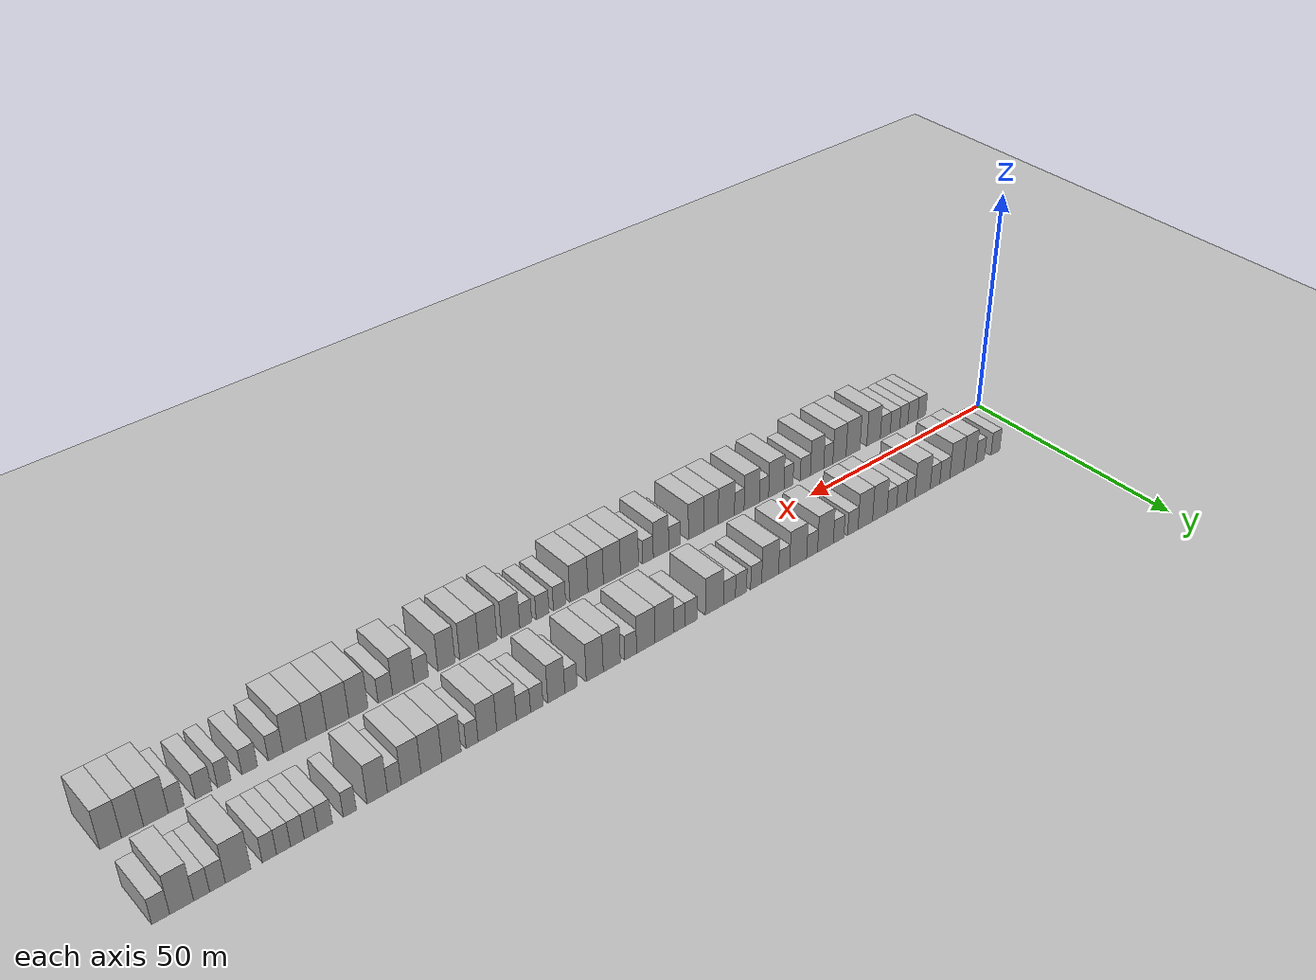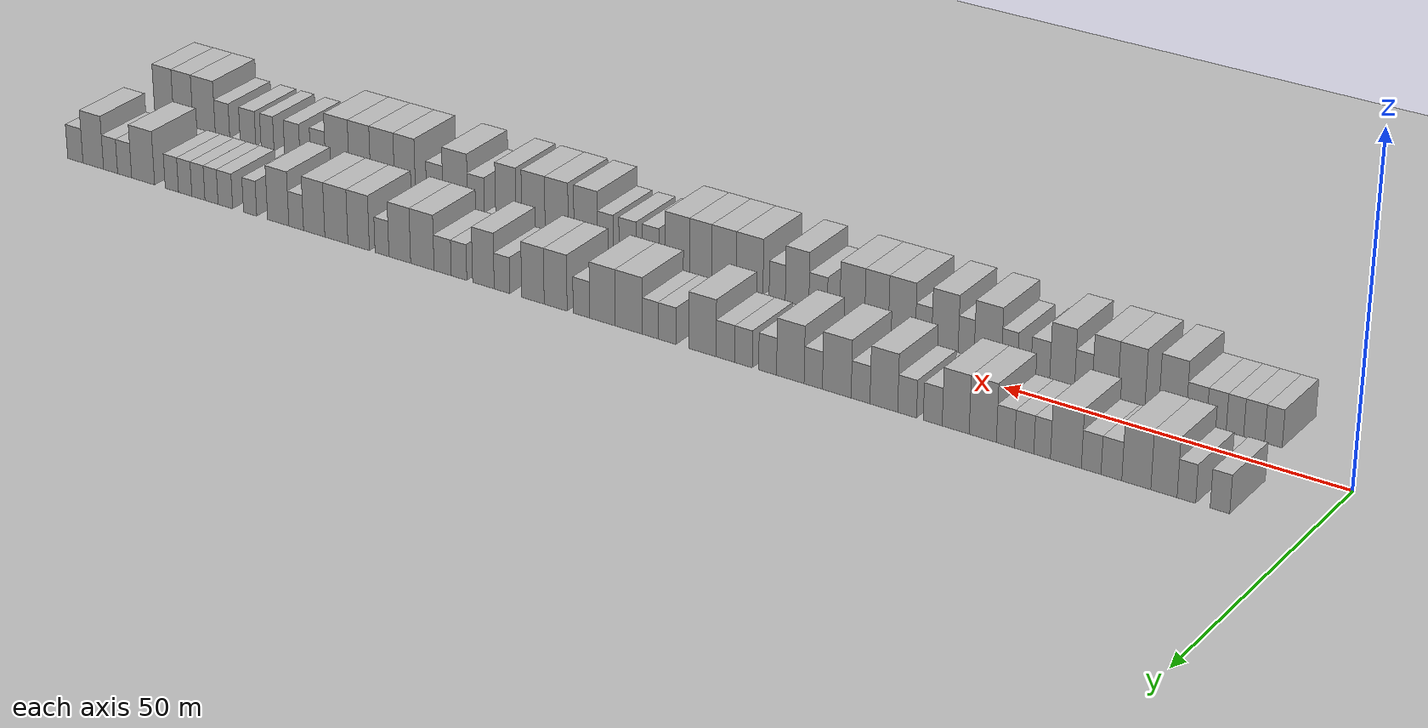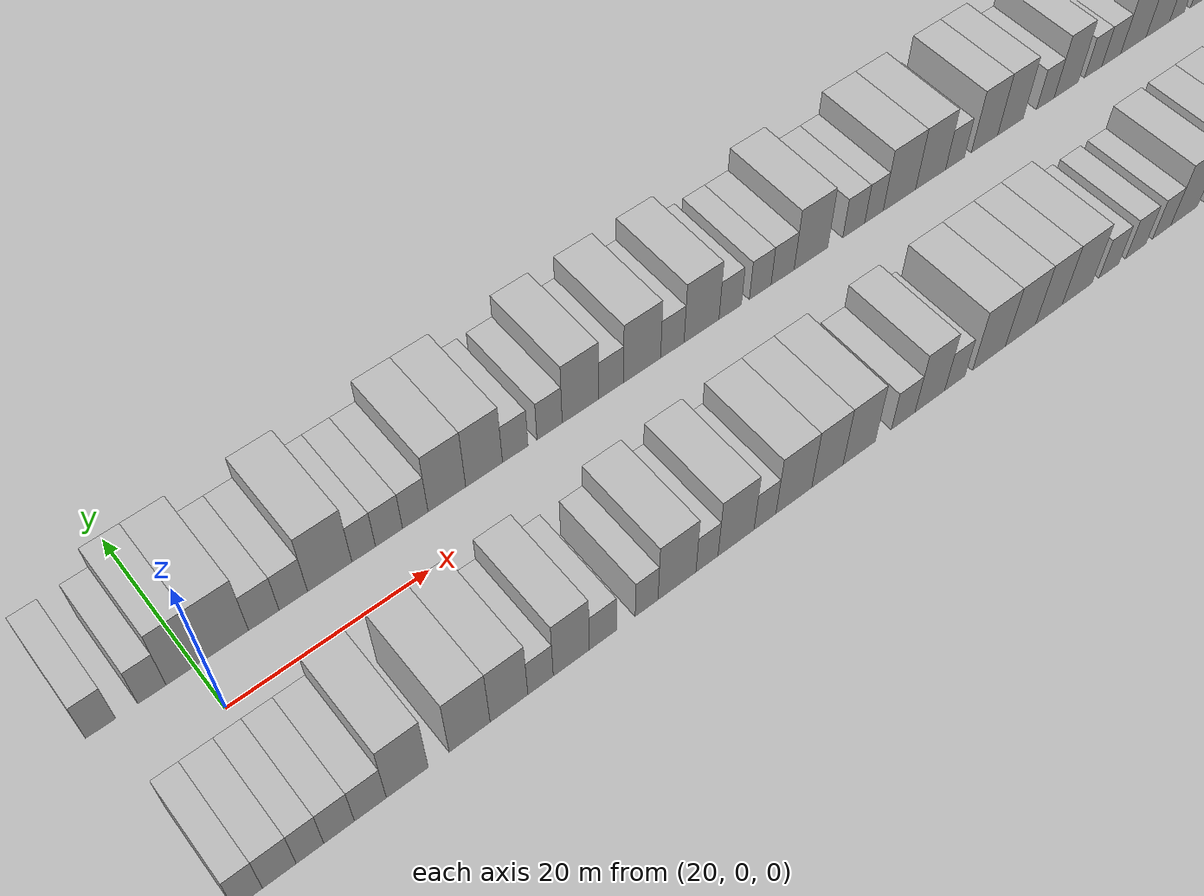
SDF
<?xml version="1.0" encoding="utf-8"?>

<sdf version="1.6">

   <world name="default">

      <gui fullscreen="0">

         <camera name="user_camera">

            <pose>-15 0 4.57585 0 0 0</pose>

            <view_controller>orbit</view_controller>

         </camera>

      </gui>

      <scene>

         <sky>

           <clouds>

             <speed>12</speed>

           </clouds>

         </sky>

         <ambient>0.4 0.4 0.4 1</ambient>

         <background>0.7 0.7 0.7 1</background>

         <shadows>1</shadows>

      </scene>

      <gravity>0 0 -9.8066</gravity>

      <magnetic_field>6e-06 2.3e-05 -4.2e-05</magnetic_field>

      <physics default="0" name="default_physics" type="ode">

         <ode>

            <solver>

               <type>quick</type>

               <iters>10</iters>

               <sor>1.0</sor>

               <use_dynamic_moi_rescaling>0</use_dynamic_moi_rescaling>

            </solver>

            <constraints>

               <cfm>0</cfm>

               <erp>0.2</erp>

               <contact_max_correcting_vel>100</contact_max_correcting_vel>

               <contact_surface_layer>0.001</contact_surface_layer>

            </constraints>

         </ode>

         <max_step_size>0.004</max_step_size>

         <real_time_factor>1</real_time_factor>

         <real_time_update_rate>250</real_time_update_rate>

      </physics>

      <light name="sun" type="directional">

         <cast_shadows>1</cast_shadows>

         <pose>0 0 10 0 0 0</pose>

         <diffuse>0.8 0.8 0.8 1</diffuse>

         <specular>0.2 0.2 0.2 1</specular>

         <attenuation>

            <range>1000</range>

            <constant>0.9</constant>

            <linear>0.01</linear>

            <quadratic>0.001</quadratic>

         </attenuation>

         <direction>-0.5 0.1 -0.9</direction>

      </light>

      <include>

         <name>ground_plane_1</name>

         <uri>model://HANNAS_ground_plane</uri>

         <pose>0 0 0  0 0 0</pose>

      </include>

      <include>

         <name>ground_plane_2</name>

         <uri>model://HANNAS_ground_plane</uri>

         <pose>100 0 0  0 0 0</pose>

      </include>

      <model name="building_1">

         <static>1</static>

         <pose frame="">11.3476 9.5000 0 0.000000 0.000000 1.570796</pose>

         <link name="link">

            <pose frame="">0 0 3.00 0 0 0</pose>

            <collision name="collision">

               <geometry>

                  <box>

                     <size>10.0000 2.6953 6.0000</size>

                  </box>

               </geometry>

               <max_contacts>10</max_contacts>

               <surface>

                  <contact>

                     <ode/>

                  </contact>

                  <bounce/>

                  <friction>

                     <torsional>

                        <ode/>

                     </torsional>

                     <ode/>

                  </friction>

               </surface>

            </collision>

            <visual name="visual">

               <cast_shadows>0</cast_shadows>

               <geometry>

                  <box>

                     <size>10.0000 2.6953 6.0000</size>

                  </box>

               </geometry>

               <material>

                  <script>

                     <uri>model://HANNAS_wall/materials/scripts</uri>

                     <uri>model://HANNAS_wall/materials/textures</uri>

                     <name>vrc/HANNAS_wall</name>

                  </script>

               </material>

            </visual>

            <self_collide>0</self_collide>

            <enable_wind>0</enable_wind>

            <kinematic>0</kinematic>

         </link>

      </model>

      <model name="building_2">

         <static>1</static>

         <pose frame="">15.9924 9.5000 0 0.000000 0.000000 1.570796</pose>

         <link name="link">

            <pose frame="">0 0 3.00 0 0 0</pose>

            <collision name="collision">

               <geometry>

                  <box>

                     <size>10.0000 2.5941 6.0000</size>

                  </box>

               </geometry>

               <max_contacts>10</max_contacts>

               <surface>

                  <contact>

                     <ode/>

                  </contact>

                  <bounce/>

                  <friction>

                     <torsional>

                        <ode/>

                     </torsional>

                     <ode/>

                  </friction>

               </surface>

            </collision>

            <visual name="visual">

               <cast_shadows>0</cast_shadows>

               <geometry>

                  <box>

                     <size>10.0000 2.5941 6.0000</size>

                  </box>

               </geometry>

               <material>

                  <script>

                     <uri>model://HANNAS_wall/materials/scripts</uri>

                     <uri>model://HANNAS_wall/materials/textures</uri>

                     <name>vrc/HANNAS_wall</name>

                  </script>

               </material>

            </visual>

            <self_collide>0</self_collide>

            <enable_wind>0</enable_wind>

            <kinematic>0</kinematic>

         </link>

      </model>

      <model name="building_3">

         <static>1</static>

         <pose frame="">19.1227 9.5000 0 0.000000 0.000000 1.570796</pose>

         <link name="link">

            <pose frame="">0 0 4.50 0 0 0</pose>

            <collision name="collision">

               <geometry>

                  <box>

                     <size>10.0000 3.6666 9.0000</size>

                  </box>

               </geometry>

               <max_contacts>10</max_contacts>

               <surface>

                  <contact>

                     <ode/>

                  </contact>

                  <bounce/>

                  <friction>

                     <torsional>

                        <ode/>

                     </torsional>

                     <ode/>

                  </friction>

               </surface>

            </collision>

            <visual name="visual">

               <cast_shadows>0</cast_shadows>

               <geometry>

                  <box>

                     <size>10.0000 3.6666 9.0000</size>

                  </box>

               </geometry>

               <material>

                  <script>

                     <uri>model://HANNAS_wall/materials/scripts</uri>

                     <uri>model://HANNAS_wall/materials/textures</uri>

                     <name>vrc/HANNAS_wall</name>

                  </script>

               </material>

            </visual>

            <self_collide>0</self_collide>

            <enable_wind>0</enable_wind>

            <kinematic>0</kinematic>

         </link>

      </model>

      <model name="building_4">

         <static>1</static>

         <pose frame="">23.0033 9.5000 0 0.000000 0.000000 1.570796</pose>

         <link name="link">

            <pose frame="">0 0 4.50 0 0 0</pose>

            <collision name="collision">

               <geometry>

                  <box>

                     <size>10.0000 4.0947 9.0000</size>

                  </box>

               </geometry>

               <max_contacts>10</max_contacts>

               <surface>

                  <contact>

                     <ode/>

                  </contact>

                  <bounce/>

                  <friction>

                     <torsional>

                        <ode/>

                     </torsional>

                     <ode/>

                  </friction>

               </surface>

            </collision>

            <visual name="visual">

               <cast_shadows>0</cast_shadows>

               <geometry>

                  <box>

                     <size>10.0000 4.0947 9.0000</size>

                  </box>

               </geometry>

               <material>

                  <script>

                     <uri>model://HANNAS_wall/materials/scripts</uri>

                     <uri>model://HANNAS_wall/materials/textures</uri>

                     <name>vrc/HANNAS_wall</name>

                  </script>

               </material>

            </visual>

            <self_collide>0</self_collide>

            <enable_wind>0</enable_wind>

            <kinematic>0</kinematic>

         </link>

      </model>

      <model name="building_5">

         <static>1</static>

         <pose frame="">26.5268 9.5000 0 0.000000 0.000000 1.570796</pose>

         <link name="link">

            <pose frame="">0 0 3.00 0 0 0</pose>

            <collision name="collision">

               <geometry>

                  <box>

                     <size>10.0000 2.9523 6.0000</size>

                  </box>

               </geometry>

               <max_contacts>10</max_contacts>

               <surface>

                  <contact>

                     <ode/>

                  </contact>

                  <bounce/>

                  <friction>

                     <torsional>

                        <ode/>

                     </torsional>

                     <ode/>

                  </friction>

               </surface>

            </collision>

            <visual name="visual">

               <cast_shadows>0</cast_shadows>

               <geometry>

                  <box>

                     <size>10.0000 2.9523 6.0000</size>

                  </box>

               </geometry>

               <material>

                  <script>

                     <uri>model://HANNAS_wall/materials/scripts</uri>

                     <uri>model://HANNAS_wall/materials/textures</uri>

                     <name>vrc/HANNAS_wall</name>

                  </script>

               </material>

            </visual>

            <self_collide>0</self_collide>

            <enable_wind>0</enable_wind>

            <kinematic>0</kinematic>

         </link>

      </model>

      <model name="building_6">

         <static>1</static>

         <pose frame="">29.4002 9.5000 0 0.000000 0.000000 1.570796</pose>

         <link name="link">

            <pose frame="">0 0 3.00 0 0 0</pose>

            <collision name="collision">

               <geometry>

                  <box>

                     <size>10.0000 2.7946 6.0000</size>

                  </box>

               </geometry>

               <max_contacts>10</max_contacts>

               <surface>

                  <contact>

                     <ode/>

                  </contact>

                  <bounce/>

                  <friction>

                     <torsional>

                        <ode/>

                     </torsional>

                     <ode/>

                  </friction>

               </surface>

            </collision>

            <visual name="visual">

               <cast_shadows>0</cast_shadows>

               <geometry>

                  <box>

                     <size>10.0000 2.7946 6.0000</size>

                  </box>

               </geometry>

               <material>

                  <script>

                     <uri>model://HANNAS_wall/materials/scripts</uri>

                     <uri>model://HANNAS_wall/materials/textures</uri>

                     <name>vrc/HANNAS_wall</name>

                  </script>

               </material>

            </visual>

            <self_collide>0</self_collide>

            <enable_wind>0</enable_wind>

            <kinematic>0</kinematic>

         </link>

      </model>

      <model name="building_7">

         <static>1</static>

         <pose frame="">33.0232 9.5000 0 0.000000 0.000000 1.570796</pose>

         <link name="link">

            <pose frame="">0 0 4.50 0 0 0</pose>

            <collision name="collision">

               <geometry>

                  <box>

                     <size>10.0000 4.4512 9.0000</size>

                  </box>

               </geometry>

               <max_contacts>10</max_contacts>

               <surface>

                  <contact>

                     <ode/>

                  </contact>

                  <bounce/>

                  <friction>

                     <torsional>

                        <ode/>

                     </torsional>

                     <ode/>

                  </friction>

               </surface>

            </collision>

            <visual name="visual">

               <cast_shadows>0</cast_shadows>

               <geometry>

                  <box>

                     <size>10.0000 4.4512 9.0000</size>

                  </box>

               </geometry>

               <material>

                  <script>

                     <uri>model://HANNAS_wall/materials/scripts</uri>

                     <uri>model://HANNAS_wall/materials/textures</uri>

                     <name>vrc/HANNAS_wall</name>

                  </script>

               </material>

            </visual>

            <self_collide>0</self_collide>

            <enable_wind>0</enable_wind>

            <kinematic>0</kinematic>

         </link>

      </model>

      <model name="building_8">

         <static>1</static>

         <pose frame="">36.4513 9.5000 0 0.000000 0.000000 1.570796</pose>

         <link name="link">

            <pose frame="">0 0 3.00 0 0 0</pose>

            <collision name="collision">

               <geometry>

                  <box>

                     <size>10.0000 2.4051 6.0000</size>

                  </box>

               </geometry>

               <max_contacts>10</max_contacts>

               <surface>

                  <contact>

                     <ode/>

                  </contact>

                  <bounce/>

                  <friction>

                     <torsional>

                        <ode/>

                     </torsional>

                     <ode/>

                  </friction>

               </surface>

            </collision>

            <visual name="visual">

               <cast_shadows>0</cast_shadows>

               <geometry>

                  <box>

                     <size>10.0000 2.4051 6.0000</size>

                  </box>

               </geometry>

               <material>

                  <script>

                     <uri>model://HANNAS_wall/materials/scripts</uri>

                     <uri>model://HANNAS_wall/materials/textures</uri>

                     <name>vrc/HANNAS_wall</name>

                  </script>

               </material>

            </visual>

            <self_collide>0</self_collide>

            <enable_wind>0</enable_wind>

            <kinematic>0</kinematic>

         </link>

      </model>

      <model name="building_9">

         <static>1</static>

         <pose frame="">39.0521 9.5000 0 0.000000 0.000000 1.570796</pose>

         <link name="link">

            <pose frame="">0 0 3.00 0 0 0</pose>

            <collision name="collision">

               <geometry>

                  <box>

                     <size>10.0000 2.7965 6.0000</size>

                  </box>

               </geometry>

               <max_contacts>10</max_contacts>

               <surface>

                  <contact>

                     <ode/>

                  </contact>

                  <bounce/>

                  <friction>

                     <torsional>

                        <ode/>

                     </torsional>

                     <ode/>

                  </friction>

               </surface>

            </collision>

            <visual name="visual">

               <cast_shadows>0</cast_shadows>

               <geometry>

                  <box>

                     <size>10.0000 2.7965 6.0000</size>

                  </box>

               </geometry>

               <material>

                  <script>

                     <uri>model://HANNAS_wall/materials/scripts</uri>

                     <uri>model://HANNAS_wall/materials/textures</uri>

                     <name>vrc/HANNAS_wall</name>

                  </script>

               </material>

            </visual>

            <self_collide>0</self_collide>

            <enable_wind>0</enable_wind>

            <kinematic>0</kinematic>

         </link>

      </model>

      <model name="building_10">

         <static>1</static>

         <pose frame="">41.7821 9.5000 0 0.000000 0.000000 1.570796</pose>

         <link name="link">

            <pose frame="">0 0 3.00 0 0 0</pose>

            <collision name="collision">

               <geometry>

                  <box>

                     <size>10.0000 2.6635 6.0000</size>

                  </box>

               </geometry>

               <max_contacts>10</max_contacts>

               <surface>

                  <contact>

                     <ode/>

                  </contact>

                  <bounce/>

                  <friction>

                     <torsional>

                        <ode/>

                     </torsional>

                     <ode/>

                  </friction>

               </surface>

            </collision>

            <visual name="visual">

               <cast_shadows>0</cast_shadows>

               <geometry>

                  <box>

                     <size>10.0000 2.6635 6.0000</size>

                  </box>

               </geometry>

               <material>

                  <script>

                     <uri>model://HANNAS_wall/materials/scripts</uri>

                     <uri>model://HANNAS_wall/materials/textures</uri>

                     <name>vrc/HANNAS_wall</name>

                  </script>

               </material>

            </visual>

            <self_collide>0</self_collide>

            <enable_wind>0</enable_wind>

            <kinematic>0</kinematic>

         </link>

      </model>

      <model name="building_11">

         <static>1</static>

         <pose frame="">45.1213 9.5000 0 0.000000 0.000000 1.570796</pose>

         <link name="link">

            <pose frame="">0 0 4.50 0 0 0</pose>

            <collision name="collision">

               <geometry>

                  <box>

                     <size>10.0000 4.0150 9.0000</size>

                  </box>

               </geometry>

               <max_contacts>10</max_contacts>

               <surface>

                  <contact>

                     <ode/>

                  </contact>

                  <bounce/>

                  <friction>

                     <torsional>

                        <ode/>

                     </torsional>

                     <ode/>

                  </friction>

               </surface>

            </collision>

            <visual name="visual">

               <cast_shadows>0</cast_shadows>

               <geometry>

                  <box>

                     <size>10.0000 4.0150 9.0000</size>

                  </box>

               </geometry>

               <material>

                  <script>

                     <uri>model://HANNAS_wall/materials/scripts</uri>

                     <uri>model://HANNAS_wall/materials/textures</uri>

                     <name>vrc/HANNAS_wall</name>

                  </script>

               </material>

            </visual>

            <self_collide>0</self_collide>

            <enable_wind>0</enable_wind>

            <kinematic>0</kinematic>

         </link>

      </model>

      <model name="building_12">

         <static>1</static>

         <pose frame="">49.1280 9.5000 0 0.000000 0.000000 1.570796</pose>

         <link name="link">

            <pose frame="">0 0 4.50 0 0 0</pose>

            <collision name="collision">

               <geometry>

                  <box>

                     <size>10.0000 3.9984 9.0000</size>

                  </box>

               </geometry>

               <max_contacts>10</max_contacts>

               <surface>

                  <contact>

                     <ode/>

                  </contact>

                  <bounce/>

                  <friction>

                     <torsional>

                        <ode/>

                     </torsional>

                     <ode/>

                  </friction>

               </surface>

            </collision>

            <visual name="visual">

               <cast_shadows>0</cast_shadows>

               <geometry>

                  <box>

                     <size>10.0000 3.9984 9.0000</size>

                  </box>

               </geometry>

               <material>

                  <script>

                     <uri>model://HANNAS_wall/materials/scripts</uri>

                     <uri>model://HANNAS_wall/materials/textures</uri>

                     <name>vrc/HANNAS_wall</name>

                  </script>

               </material>

            </visual>

            <self_collide>0</self_collide>

            <enable_wind>0</enable_wind>

            <kinematic>0</kinematic>

         </link>

      </model>

      <model name="building_13">

         <static>1</static>

         <pose frame="">52.5361 9.5000 0 0.000000 0.000000 1.570796</pose>

         <link name="link">

            <pose frame="">0 0 3.00 0 0 0</pose>

            <collision name="collision">

               <geometry>

                  <box>

                     <size>10.0000 2.8178 6.0000</size>

                  </box>

               </geometry>

               <max_contacts>10</max_contacts>

               <surface>

                  <contact>

                     <ode/>

                  </contact>

                  <bounce/>

                  <friction>

                     <torsional>

                        <ode/>

                     </torsional>

                     <ode/>

                  </friction>

               </surface>

            </collision>

            <visual name="visual">

               <cast_shadows>0</cast_shadows>

               <geometry>

                  <box>

                     <size>10.0000 2.8178 6.0000</size>

                  </box>

               </geometry>

               <material>

                  <script>

                     <uri>model://HANNAS_wall/materials/scripts</uri>

                     <uri>model://HANNAS_wall/materials/textures</uri>

                     <name>vrc/HANNAS_wall</name>

                  </script>

               </material>

            </visual>

            <self_collide>0</self_collide>

            <enable_wind>0</enable_wind>

            <kinematic>0</kinematic>

         </link>

      </model>

      <model name="building_14">

         <static>1</static>

         <pose frame="">56.3678 9.5000 0 0.000000 0.000000 1.570796</pose>

         <link name="link">

            <pose frame="">0 0 3.00 0 0 0</pose>

            <collision name="collision">

               <geometry>

                  <box>

                     <size>10.0000 2.8456 6.0000</size>

                  </box>

               </geometry>

               <max_contacts>10</max_contacts>

               <surface>

                  <contact>

                     <ode/>

                  </contact>

                  <bounce/>

                  <friction>

                     <torsional>

                        <ode/>

                     </torsional>

                     <ode/>

                  </friction>

               </surface>

            </collision>

            <visual name="visual">

               <cast_shadows>0</cast_shadows>

               <geometry>

                  <box>

                     <size>10.0000 2.8456 6.0000</size>

                  </box>

               </geometry>

               <material>

                  <script>

                     <uri>model://HANNAS_wall/materials/scripts</uri>

                     <uri>model://HANNAS_wall/materials/textures</uri>

                     <name>vrc/HANNAS_wall</name>

                  </script>

               </material>

            </visual>

            <self_collide>0</self_collide>

            <enable_wind>0</enable_wind>

            <kinematic>0</kinematic>

         </link>

      </model>

      <model name="building_15">

         <static>1</static>

         <pose frame="">59.8901 9.5000 0 0.000000 0.000000 1.570796</pose>

         <link name="link">

            <pose frame="">0 0 4.50 0 0 0</pose>

            <collision name="collision">

               <geometry>

                  <box>

                     <size>10.0000 4.1991 9.0000</size>

                  </box>

               </geometry>

               <max_contacts>10</max_contacts>

               <surface>

                  <contact>

                     <ode/>

                  </contact>

                  <bounce/>

                  <friction>

                     <torsional>

                        <ode/>

                     </torsional>

                     <ode/>

                  </friction>

               </surface>

            </collision>

            <visual name="visual">

               <cast_shadows>0</cast_shadows>

               <geometry>

                  <box>

                     <size>10.0000 4.1991 9.0000</size>

                  </box>

               </geometry>

               <material>

                  <script>

                     <uri>model://HANNAS_wall/materials/scripts</uri>

                     <uri>model://HANNAS_wall/materials/textures</uri>

                     <name>vrc/HANNAS_wall</name>

                  </script>

               </material>

            </visual>

            <self_collide>0</self_collide>

            <enable_wind>0</enable_wind>

            <kinematic>0</kinematic>

         </link>

      </model>

      <model name="building_16">

         <static>1</static>

         <pose frame="">63.4212 9.5000 0 0.000000 0.000000 1.570796</pose>

         <link name="link">

            <pose frame="">0 0 3.00 0 0 0</pose>

            <collision name="collision">

               <geometry>

                  <box>

                     <size>10.0000 2.8630 6.0000</size>

                  </box>

               </geometry>

               <max_contacts>10</max_contacts>

               <surface>

                  <contact>

                     <ode/>

                  </contact>

                  <bounce/>

                  <friction>

                     <torsional>

                        <ode/>

                     </torsional>

                     <ode/>

                  </friction>

               </surface>

            </collision>

            <visual name="visual">

               <cast_shadows>0</cast_shadows>

               <geometry>

                  <box>

                     <size>10.0000 2.8630 6.0000</size>

                  </box>

               </geometry>

               <material>

                  <script>

                     <uri>model://HANNAS_wall/materials/scripts</uri>

                     <uri>model://HANNAS_wall/materials/textures</uri>

                     <name>vrc/HANNAS_wall</name>

                  </script>

               </material>

            </visual>

            <self_collide>0</self_collide>

            <enable_wind>0</enable_wind>

            <kinematic>0</kinematic>

         </link>

      </model>

      <model name="building_17">

         <static>1</static>

         <pose frame="">67.0569 9.5000 0 0.000000 0.000000 1.570796</pose>

         <link name="link">

            <pose frame="">0 0 4.50 0 0 0</pose>

            <collision name="collision">

               <geometry>

                  <box>

                     <size>10.0000 4.4085 9.0000</size>

                  </box>

               </geometry>

               <max_contacts>10</max_contacts>

               <surface>

                  <contact>

                     <ode/>

                  </contact>

                  <bounce/>

                  <friction>

                     <torsional>

                        <ode/>

                     </torsional>

                     <ode/>

                  </friction>

               </surface>

            </collision>

            <visual name="visual">

               <cast_shadows>0</cast_shadows>

               <geometry>

                  <box>

                     <size>10.0000 4.4085 9.0000</size>

                  </box>

               </geometry>

               <material>

                  <script>

                     <uri>model://HANNAS_wall/materials/scripts</uri>

                     <uri>model://HANNAS_wall/materials/textures</uri>

                     <name>vrc/HANNAS_wall</name>

                  </script>

               </material>

            </visual>

            <self_collide>0</self_collide>

            <enable_wind>0</enable_wind>

            <kinematic>0</kinematic>

         </link>

      </model>

      <model name="building_18">

         <static>1</static>

         <pose frame="">70.6775 9.5000 0 0.000000 0.000000 1.570796</pose>

         <link name="link">

            <pose frame="">0 0 3.00 0 0 0</pose>

            <collision name="collision">

               <geometry>

                  <box>

                     <size>10.0000 2.8328 6.0000</size>

                  </box>

               </geometry>

               <max_contacts>10</max_contacts>

               <surface>

                  <contact>

                     <ode/>

                  </contact>

                  <bounce/>

                  <friction>

                     <torsional>

                        <ode/>

                     </torsional>

                     <ode/>

                  </friction>

               </surface>

            </collision>

            <visual name="visual">

               <cast_shadows>0</cast_shadows>

               <geometry>

                  <box>

                     <size>10.0000 2.8328 6.0000</size>

                  </box>

               </geometry>

               <material>

                  <script>

                     <uri>model://HANNAS_wall/materials/scripts</uri>

                     <uri>model://HANNAS_wall/materials/textures</uri>

                     <name>vrc/HANNAS_wall</name>

                  </script>

               </material>

            </visual>

            <self_collide>0</self_collide>

            <enable_wind>0</enable_wind>

            <kinematic>0</kinematic>

         </link>

      </model>

      <model name="building_19">

         <static>1</static>

         <pose frame="">74.2370 9.5000 0 0.000000 0.000000 1.570796</pose>

         <link name="link">

            <pose frame="">0 0 4.50 0 0 0</pose>

            <collision name="collision">

               <geometry>

                  <box>

                     <size>10.0000 4.2862 9.0000</size>

                  </box>

               </geometry>

               <max_contacts>10</max_contacts>

               <surface>

                  <contact>

                     <ode/>

                  </contact>

                  <bounce/>

                  <friction>

                     <torsional>

                        <ode/>

                     </torsional>

                     <ode/>

                  </friction>

               </surface>

            </collision>

            <visual name="visual">

               <cast_shadows>0</cast_shadows>

               <geometry>

                  <box>

                     <size>10.0000 4.2862 9.0000</size>

                  </box>

               </geometry>

               <material>

                  <script>

                     <uri>model://HANNAS_wall/materials/scripts</uri>

                     <uri>model://HANNAS_wall/materials/textures</uri>

                     <name>vrc/HANNAS_wall</name>

                  </script>

               </material>

            </visual>

            <self_collide>0</self_collide>

            <enable_wind>0</enable_wind>

            <kinematic>0</kinematic>

         </link>

      </model>

      <model name="building_20">

         <static>1</static>

         <pose frame="">77.7793 9.5000 0 0.000000 0.000000 1.570796</pose>

         <link name="link">

            <pose frame="">0 0 3.00 0 0 0</pose>

            <collision name="collision">

               <geometry>

                  <box>

                     <size>10.0000 2.7983 6.0000</size>

                  </box>

               </geometry>

               <max_contacts>10</max_contacts>

               <surface>

                  <contact>

                     <ode/>

                  </contact>

                  <bounce/>

                  <friction>

                     <torsional>

                        <ode/>

                     </torsional>

                     <ode/>

                  </friction>

               </surface>

            </collision>

            <visual name="visual">

               <cast_shadows>0</cast_shadows>

               <geometry>

                  <box>

                     <size>10.0000 2.7983 6.0000</size>

                  </box>

               </geometry>

               <material>

                  <script>

                     <uri>model://HANNAS_wall/materials/scripts</uri>

                     <uri>model://HANNAS_wall/materials/textures</uri>

                     <name>vrc/HANNAS_wall</name>

                  </script>

               </material>

            </visual>

            <self_collide>0</self_collide>

            <enable_wind>0</enable_wind>

            <kinematic>0</kinematic>

         </link>

      </model>

      <model name="building_21">

         <static>1</static>

         <pose frame="">81.5589 9.5000 0 0.000000 0.000000 1.570796</pose>

         <link name="link">

            <pose frame="">0 0 3.00 0 0 0</pose>

            <collision name="collision">

               <geometry>

                  <box>

                     <size>10.0000 2.7608 6.0000</size>

                  </box>

               </geometry>

               <max_contacts>10</max_contacts>

               <surface>

                  <contact>

                     <ode/>

                  </contact>

                  <bounce/>

                  <friction>

                     <torsional>

                        <ode/>

                     </torsional>

                     <ode/>

                  </friction>

               </surface>

            </collision>

            <visual name="visual">

               <cast_shadows>0</cast_shadows>

               <geometry>

                  <box>

                     <size>10.0000 2.7608 6.0000</size>

                  </box>

               </geometry>

               <material>

                  <script>

                     <uri>model://HANNAS_wall/materials/scripts</uri>

                     <uri>model://HANNAS_wall/materials/textures</uri>

                     <name>vrc/HANNAS_wall</name>

                  </script>

               </material>

            </visual>

            <self_collide>0</self_collide>

            <enable_wind>0</enable_wind>

            <kinematic>0</kinematic>

         </link>

      </model>

      <model name="building_22">

         <static>1</static>

         <pose frame="">84.4221 9.5000 0 0.000000 0.000000 1.570796</pose>

         <link name="link">

            <pose frame="">0 0 3.00 0 0 0</pose>

            <collision name="collision">

               <geometry>

                  <box>

                     <size>10.0000 2.9657 6.0000</size>

                  </box>

               </geometry>

               <max_contacts>10</max_contacts>

               <surface>

                  <contact>

                     <ode/>

                  </contact>

                  <bounce/>

                  <friction>

                     <torsional>

                        <ode/>

                     </torsional>

                     <ode/>

                  </friction>

               </surface>

            </collision>

            <visual name="visual">

               <cast_shadows>0</cast_shadows>

               <geometry>

                  <box>

                     <size>10.0000 2.9657 6.0000</size>

                  </box>

               </geometry>

               <material>

                  <script>

                     <uri>model://HANNAS_wall/materials/scripts</uri>

                     <uri>model://HANNAS_wall/materials/textures</uri>

                     <name>vrc/HANNAS_wall</name>

                  </script>

               </material>

            </visual>

            <self_collide>0</self_collide>

            <enable_wind>0</enable_wind>

            <kinematic>0</kinematic>

         </link>

      </model>

      <model name="building_23">

         <static>1</static>

         <pose frame="">88.1063 9.5000 0 0.000000 0.000000 1.570796</pose>

         <link name="link">

            <pose frame="">0 0 4.50 0 0 0</pose>

            <collision name="collision">

               <geometry>

                  <box>

                     <size>10.0000 4.4028 9.0000</size>

                  </box>

               </geometry>

               <max_contacts>10</max_contacts>

               <surface>

                  <contact>

                     <ode/>

                  </contact>

                  <bounce/>

                  <friction>

                     <torsional>

                        <ode/>

                     </torsional>

                     <ode/>

                  </friction>

               </surface>

            </collision>

            <visual name="visual">

               <cast_shadows>0</cast_shadows>

               <geometry>

                  <box>

                     <size>10.0000 4.4028 9.0000</size>

                  </box>

               </geometry>

               <material>

                  <script>

                     <uri>model://HANNAS_wall/materials/scripts</uri>

                     <uri>model://HANNAS_wall/materials/textures</uri>

                     <name>vrc/HANNAS_wall</name>

                  </script>

               </material>

            </visual>

            <self_collide>0</self_collide>

            <enable_wind>0</enable_wind>

            <kinematic>0</kinematic>

         </link>

      </model>

      <model name="building_24">

         <static>1</static>

         <pose frame="">93.7768 9.5000 0 0.000000 0.000000 1.570796</pose>

         <link name="link">

            <pose frame="">0 0 3.00 0 0 0</pose>

            <collision name="collision">

               <geometry>

                  <box>

                     <size>10.0000 2.9382 6.0000</size>

                  </box>

               </geometry>

               <max_contacts>10</max_contacts>

               <surface>

                  <contact>

                     <ode/>

                  </contact>

                  <bounce/>

                  <friction>

                     <torsional>

                        <ode/>

                     </torsional>

                     <ode/>

                  </friction>

               </surface>

            </collision>

            <visual name="visual">

               <cast_shadows>0</cast_shadows>

               <geometry>

                  <box>

                     <size>10.0000 2.9382 6.0000</size>

                  </box>

               </geometry>

               <material>

                  <script>

                     <uri>model://HANNAS_wall/materials/scripts</uri>

                     <uri>model://HANNAS_wall/materials/textures</uri>

                     <name>vrc/HANNAS_wall</name>

                  </script>

               </material>

            </visual>

            <self_collide>0</self_collide>

            <enable_wind>0</enable_wind>

            <kinematic>0</kinematic>

         </link>

      </model>

      <model name="building_25">

         <static>1</static>

         <pose frame="">96.4989 9.5000 0 0.000000 0.000000 1.570796</pose>

         <link name="link">

            <pose frame="">0 0 3.00 0 0 0</pose>

            <collision name="collision">

               <geometry>

                  <box>

                     <size>10.0000 2.5060 6.0000</size>

                  </box>

               </geometry>

               <max_contacts>10</max_contacts>

               <surface>

                  <contact>

                     <ode/>

                  </contact>

                  <bounce/>

                  <friction>

                     <torsional>

                        <ode/>

                     </torsional>

                     <ode/>

                  </friction>

               </surface>

            </collision>

            <visual name="visual">

               <cast_shadows>0</cast_shadows>

               <geometry>

                  <box>

                     <size>10.0000 2.5060 6.0000</size>

                  </box>

               </geometry>

               <material>

                  <script>

                     <uri>model://HANNAS_wall/materials/scripts</uri>

                     <uri>model://HANNAS_wall/materials/textures</uri>

                     <name>vrc/HANNAS_wall</name>

                  </script>

               </material>

            </visual>

            <self_collide>0</self_collide>

            <enable_wind>0</enable_wind>

            <kinematic>0</kinematic>

         </link>

      </model>

      <model name="building_26">

         <static>1</static>

         <pose frame="">99.9902 9.5000 0 0.000000 0.000000 1.570796</pose>

         <link name="link">

            <pose frame="">0 0 4.50 0 0 0</pose>

            <collision name="collision">

               <geometry>

                  <box>

                     <size>10.0000 4.4765 9.0000</size>

                  </box>

               </geometry>

               <max_contacts>10</max_contacts>

               <surface>

                  <contact>

                     <ode/>

                  </contact>

                  <bounce/>

                  <friction>

                     <torsional>

                        <ode/>

                     </torsional>

                     <ode/>

                  </friction>

               </surface>

            </collision>

            <visual name="visual">

               <cast_shadows>0</cast_shadows>

               <geometry>

                  <box>

                     <size>10.0000 4.4765 9.0000</size>

                  </box>

               </geometry>

               <material>

                  <script>

                     <uri>model://HANNAS_wall/materials/scripts</uri>

                     <uri>model://HANNAS_wall/materials/textures</uri>

                     <name>vrc/HANNAS_wall</name>

                  </script>

               </material>

            </visual>

            <self_collide>0</self_collide>

            <enable_wind>0</enable_wind>

            <kinematic>0</kinematic>

         </link>

      </model>

      <model name="building_27">

         <static>1</static>

         <pose frame="">104.3361 9.5000 0 0.000000 0.000000 1.570796</pose>

         <link name="link">

            <pose frame="">0 0 4.50 0 0 0</pose>

            <collision name="collision">

               <geometry>

                  <box>

                     <size>10.0000 4.2153 9.0000</size>

                  </box>

               </geometry>

               <max_contacts>10</max_contacts>

               <surface>

                  <contact>

                     <ode/>

                  </contact>

                  <bounce/>

                  <friction>

                     <torsional>

                        <ode/>

                     </torsional>

                     <ode/>

                  </friction>

               </surface>

            </collision>

            <visual name="visual">

               <cast_shadows>0</cast_shadows>

               <geometry>

                  <box>

                     <size>10.0000 4.2153 9.0000</size>

                  </box>

               </geometry>

               <material>

                  <script>

                     <uri>model://HANNAS_wall/materials/scripts</uri>

                     <uri>model://HANNAS_wall/materials/textures</uri>

                     <name>vrc/HANNAS_wall</name>

                  </script>

               </material>

            </visual>

            <self_collide>0</self_collide>

            <enable_wind>0</enable_wind>

            <kinematic>0</kinematic>

         </link>

      </model>

      <model name="building_28">

         <static>1</static>

         <pose frame="">107.7985 9.5000 0 0.000000 0.000000 1.570796</pose>

         <link name="link">

            <pose frame="">0 0 3.00 0 0 0</pose>

            <collision name="collision">

               <geometry>

                  <box>

                     <size>10.0000 2.7095 6.0000</size>

                  </box>

               </geometry>

               <max_contacts>10</max_contacts>

               <surface>

                  <contact>

                     <ode/>

                  </contact>

                  <bounce/>

                  <friction>

                     <torsional>

                        <ode/>

                     </torsional>

                     <ode/>

                  </friction>

               </surface>

            </collision>

            <visual name="visual">

               <cast_shadows>0</cast_shadows>

               <geometry>

                  <box>

                     <size>10.0000 2.7095 6.0000</size>

                  </box>

               </geometry>

               <material>

                  <script>

                     <uri>model://HANNAS_wall/materials/scripts</uri>

                     <uri>model://HANNAS_wall/materials/textures</uri>

                     <name>vrc/HANNAS_wall</name>

                  </script>

               </material>

            </visual>

            <self_collide>0</self_collide>

            <enable_wind>0</enable_wind>

            <kinematic>0</kinematic>

         </link>

      </model>

      <model name="building_29">

         <static>1</static>

         <pose frame="">112.0687 9.5000 0 0.000000 0.000000 1.570796</pose>

         <link name="link">

            <pose frame="">0 0 4.50 0 0 0</pose>

            <collision name="collision">

               <geometry>

                  <box>

                     <size>10.0000 3.8309 9.0000</size>

                  </box>

               </geometry>

               <max_contacts>10</max_contacts>

               <surface>

                  <contact>

                     <ode/>

                  </contact>

                  <bounce/>

                  <friction>

                     <torsional>

                        <ode/>

                     </torsional>

                     <ode/>

                  </friction>

               </surface>

            </collision>

            <visual name="visual">

               <cast_shadows>0</cast_shadows>

               <geometry>

                  <box>

                     <size>10.0000 3.8309 9.0000</size>

                  </box>

               </geometry>

               <material>

                  <script>

                     <uri>model://HANNAS_wall/materials/scripts</uri>

                     <uri>model://HANNAS_wall/materials/textures</uri>

                     <name>vrc/HANNAS_wall</name>

                  </script>

               </material>

            </visual>

            <self_collide>0</self_collide>

            <enable_wind>0</enable_wind>

            <kinematic>0</kinematic>

         </link>

      </model>

      <model name="building_30">

         <static>1</static>

         <pose frame="">115.8714 9.5000 0 0.000000 0.000000 1.570796</pose>

         <link name="link">

            <pose frame="">0 0 4.50 0 0 0</pose>

            <collision name="collision">

               <geometry>

                  <box>

                     <size>10.0000 3.7743 9.0000</size>

                  </box>

               </geometry>

               <max_contacts>10</max_contacts>

               <surface>

                  <contact>

                     <ode/>

                  </contact>

                  <bounce/>

                  <friction>

                     <torsional>

                        <ode/>

                     </torsional>

                     <ode/>

                  </friction>

               </surface>

            </collision>

            <visual name="visual">

               <cast_shadows>0</cast_shadows>

               <geometry>

                  <box>

                     <size>10.0000 3.7743 9.0000</size>

                  </box>

               </geometry>

               <material>

                  <script>

                     <uri>model://HANNAS_wall/materials/scripts</uri>

                     <uri>model://HANNAS_wall/materials/textures</uri>

                     <name>vrc/HANNAS_wall</name>

                  </script>

               </material>

            </visual>

            <self_collide>0</self_collide>

            <enable_wind>0</enable_wind>

            <kinematic>0</kinematic>

         </link>

      </model>

      <model name="building_31">

         <static>1</static>

         <pose frame="">121.0918 9.5000 0 0.000000 0.000000 1.570796</pose>

         <link name="link">

            <pose frame="">0 0 3.00 0 0 0</pose>

            <collision name="collision">

               <geometry>

                  <box>

                     <size>10.0000 2.6666 6.0000</size>

                  </box>

               </geometry>

               <max_contacts>10</max_contacts>

               <surface>

                  <contact>

                     <ode/>

                  </contact>

                  <bounce/>

                  <friction>

                     <torsional>

                        <ode/>

                     </torsional>

                     <ode/>

                  </friction>

               </surface>

            </collision>

            <visual name="visual">

               <cast_shadows>0</cast_shadows>

               <geometry>

                  <box>

                     <size>10.0000 2.6666 6.0000</size>

                  </box>

               </geometry>

               <material>

                  <script>

                     <uri>model://HANNAS_wall/materials/scripts</uri>

                     <uri>model://HANNAS_wall/materials/textures</uri>

                     <name>vrc/HANNAS_wall</name>

                  </script>

               </material>

            </visual>

            <self_collide>0</self_collide>

            <enable_wind>0</enable_wind>

            <kinematic>0</kinematic>

         </link>

      </model>

      <model name="building_32">

         <static>1</static>

         <pose frame="">124.2639 9.5000 0 0.000000 0.000000 1.570796</pose>

         <link name="link">

            <pose frame="">0 0 4.50 0 0 0</pose>

            <collision name="collision">

               <geometry>

                  <box>

                     <size>10.0000 3.6775 9.0000</size>

                  </box>

               </geometry>

               <max_contacts>10</max_contacts>

               <surface>

                  <contact>

                     <ode/>

                  </contact>

                  <bounce/>

                  <friction>

                     <torsional>

                        <ode/>

                     </torsional>

                     <ode/>

                  </friction>

               </surface>

            </collision>

            <visual name="visual">

               <cast_shadows>0</cast_shadows>

               <geometry>

                  <box>

                     <size>10.0000 3.6775 9.0000</size>

                  </box>

               </geometry>

               <material>

                  <script>

                     <uri>model://HANNAS_wall/materials/scripts</uri>

                     <uri>model://HANNAS_wall/materials/textures</uri>

                     <name>vrc/HANNAS_wall</name>

                  </script>

               </material>

            </visual>

            <self_collide>0</self_collide>

            <enable_wind>0</enable_wind>

            <kinematic>0</kinematic>

         </link>

      </model>

      <model name="building_33">

         <static>1</static>

         <pose frame="">128.4353 9.5000 0 0.000000 0.000000 1.570796</pose>

         <link name="link">

            <pose frame="">0 0 3.00 0 0 0</pose>

            <collision name="collision">

               <geometry>

                  <box>

                     <size>10.0000 2.6653 6.0000</size>

                  </box>

               </geometry>

               <max_contacts>10</max_contacts>

               <surface>

                  <contact>

                     <ode/>

                  </contact>

                  <bounce/>

                  <friction>

                     <torsional>

                        <ode/>

                     </torsional>

                     <ode/>

                  </friction>

               </surface>

            </collision>

            <visual name="visual">

               <cast_shadows>0</cast_shadows>

               <geometry>

                  <box>

                     <size>10.0000 2.6653 6.0000</size>

                  </box>

               </geometry>

               <material>

                  <script>

                     <uri>model://HANNAS_wall/materials/scripts</uri>

                     <uri>model://HANNAS_wall/materials/textures</uri>

                     <name>vrc/HANNAS_wall</name>

                  </script>

               </material>

            </visual>

            <self_collide>0</self_collide>

            <enable_wind>0</enable_wind>

            <kinematic>0</kinematic>

         </link>

      </model>

      <model name="building_34">

         <static>1</static>

         <pose frame="">131.2586 9.5000 0 0.000000 0.000000 1.570796</pose>

         <link name="link">

            <pose frame="">0 0 3.00 0 0 0</pose>

            <collision name="collision">

               <geometry>

                  <box>

                     <size>10.0000 2.9811 6.0000</size>

                  </box>

               </geometry>

               <max_contacts>10</max_contacts>

               <surface>

                  <contact>

                     <ode/>

                  </contact>

                  <bounce/>

                  <friction>

                     <torsional>

                        <ode/>

                     </torsional>

                     <ode/>

                  </friction>

               </surface>

            </collision>

            <visual name="visual">

               <cast_shadows>0</cast_shadows>

               <geometry>

                  <box>

                     <size>10.0000 2.9811 6.0000</size>

                  </box>

               </geometry>

               <material>

                  <script>

                     <uri>model://HANNAS_wall/materials/scripts</uri>

                     <uri>model://HANNAS_wall/materials/textures</uri>

                     <name>vrc/HANNAS_wall</name>

                  </script>

               </material>

            </visual>

            <self_collide>0</self_collide>

            <enable_wind>0</enable_wind>

            <kinematic>0</kinematic>

         </link>

      </model>

      <model name="building_35">

         <static>1</static>

         <pose frame="">134.7877 9.5000 0 0.000000 0.000000 1.570796</pose>

         <link name="link">

            <pose frame="">0 0 4.50 0 0 0</pose>

            <collision name="collision">

               <geometry>

                  <box>

                     <size>10.0000 4.0771 9.0000</size>

                  </box>

               </geometry>

               <max_contacts>10</max_contacts>

               <surface>

                  <contact>

                     <ode/>

                  </contact>

                  <bounce/>

                  <friction>

                     <torsional>

                        <ode/>

                     </torsional>

                     <ode/>

                  </friction>

               </surface>

            </collision>

            <visual name="visual">

               <cast_shadows>0</cast_shadows>

               <geometry>

                  <box>

                     <size>10.0000 4.0771 9.0000</size>

                  </box>

               </geometry>

               <material>

                  <script>

                     <uri>model://HANNAS_wall/materials/scripts</uri>

                     <uri>model://HANNAS_wall/materials/textures</uri>

                     <name>vrc/HANNAS_wall</name>

                  </script>

               </material>

            </visual>

            <self_collide>0</self_collide>

            <enable_wind>0</enable_wind>

            <kinematic>0</kinematic>

         </link>

      </model>

      <model name="building_36">

         <static>1</static>

         <pose frame="">138.7302 9.5000 0 0.000000 0.000000 1.570796</pose>

         <link name="link">

            <pose frame="">0 0 4.50 0 0 0</pose>

            <collision name="collision">

               <geometry>

                  <box>

                     <size>10.0000 3.8079 9.0000</size>

                  </box>

               </geometry>

               <max_contacts>10</max_contacts>

               <surface>

                  <contact>

                     <ode/>

                  </contact>

                  <bounce/>

                  <friction>

                     <torsional>

                        <ode/>

                     </torsional>

                     <ode/>

                  </friction>

               </surface>

            </collision>

            <visual name="visual">

               <cast_shadows>0</cast_shadows>

               <geometry>

                  <box>

                     <size>10.0000 3.8079 9.0000</size>

                  </box>

               </geometry>

               <material>

                  <script>

                     <uri>model://HANNAS_wall/materials/scripts</uri>

                     <uri>model://HANNAS_wall/materials/textures</uri>

                     <name>vrc/HANNAS_wall</name>

                  </script>

               </material>

            </visual>

            <self_collide>0</self_collide>

            <enable_wind>0</enable_wind>

            <kinematic>0</kinematic>

         </link>

      </model>

      <model name="building_37">

         <static>1</static>

         <pose frame="">141.8558 9.5000 0 0.000000 0.000000 1.570796</pose>

         <link name="link">

            <pose frame="">0 0 3.00 0 0 0</pose>

            <collision name="collision">

               <geometry>

                  <box>

                     <size>10.0000 2.4435 6.0000</size>

                  </box>

               </geometry>

               <max_contacts>10</max_contacts>

               <surface>

                  <contact>

                     <ode/>

                  </contact>

                  <bounce/>

                  <friction>

                     <torsional>

                        <ode/>

                     </torsional>

                     <ode/>

                  </friction>

               </surface>

            </collision>

            <visual name="visual">

               <cast_shadows>0</cast_shadows>

               <geometry>

                  <box>

                     <size>10.0000 2.4435 6.0000</size>

                  </box>

               </geometry>

               <material>

                  <script>

                     <uri>model://HANNAS_wall/materials/scripts</uri>

                     <uri>model://HANNAS_wall/materials/textures</uri>

                     <name>vrc/HANNAS_wall</name>

                  </script>

               </material>

            </visual>

            <self_collide>0</self_collide>

            <enable_wind>0</enable_wind>

            <kinematic>0</kinematic>

         </link>

      </model>

      <model name="building_38">

         <static>1</static>

         <pose frame="">145.9824 9.5000 0 0.000000 0.000000 1.570796</pose>

         <link name="link">

            <pose frame="">0 0 4.50 0 0 0</pose>

            <collision name="collision">

               <geometry>

                  <box>

                     <size>10.0000 3.8097 9.0000</size>

                  </box>

               </geometry>

               <max_contacts>10</max_contacts>

               <surface>

                  <contact>

                     <ode/>

                  </contact>

                  <bounce/>

                  <friction>

                     <torsional>

                        <ode/>

                     </torsional>

                     <ode/>

                  </friction>

               </surface>

            </collision>

            <visual name="visual">

               <cast_shadows>0</cast_shadows>

               <geometry>

                  <box>

                     <size>10.0000 3.8097 9.0000</size>

                  </box>

               </geometry>

               <material>

                  <script>

                     <uri>model://HANNAS_wall/materials/scripts</uri>

                     <uri>model://HANNAS_wall/materials/textures</uri>

                     <name>vrc/HANNAS_wall</name>

                  </script>

               </material>

            </visual>

            <self_collide>0</self_collide>

            <enable_wind>0</enable_wind>

            <kinematic>0</kinematic>

         </link>

      </model>

      <model name="building_39">

         <static>1</static>

         <pose frame="">149.9508 9.5000 0 0.000000 0.000000 1.570796</pose>

         <link name="link">

            <pose frame="">0 0 4.50 0 0 0</pose>

            <collision name="collision">

               <geometry>

                  <box>

                     <size>10.0000 4.1271 9.0000</size>

                  </box>

               </geometry>

               <max_contacts>10</max_contacts>

               <surface>

                  <contact>

                     <ode/>

                  </contact>

                  <bounce/>

                  <friction>

                     <torsional>

                        <ode/>

                     </torsional>

                     <ode/>

                  </friction>

               </surface>

            </collision>

            <visual name="visual">

               <cast_shadows>0</cast_shadows>

               <geometry>

                  <box>

                     <size>10.0000 4.1271 9.0000</size>

                  </box>

               </geometry>

               <material>

                  <script>

                     <uri>model://HANNAS_wall/materials/scripts</uri>

                     <uri>model://HANNAS_wall/materials/textures</uri>

                     <name>vrc/HANNAS_wall</name>

                  </script>

               </material>

            </visual>

            <self_collide>0</self_collide>

            <enable_wind>0</enable_wind>

            <kinematic>0</kinematic>

         </link>

      </model>

      <model name="building_40">

         <static>1</static>

         <pose frame="">153.9296 9.5000 0 0.000000 0.000000 1.570796</pose>

         <link name="link">

            <pose frame="">0 0 4.50 0 0 0</pose>

            <collision name="collision">

               <geometry>

                  <box>

                     <size>10.0000 3.8306 9.0000</size>

                  </box>

               </geometry>

               <max_contacts>10</max_contacts>

               <surface>

                  <contact>

                     <ode/>

                  </contact>

                  <bounce/>

                  <friction>

                     <torsional>

                        <ode/>

                     </torsional>

                     <ode/>

                  </friction>

               </surface>

            </collision>

            <visual name="visual">

               <cast_shadows>0</cast_shadows>

               <geometry>

                  <box>

                     <size>10.0000 3.8306 9.0000</size>

                  </box>

               </geometry>

               <material>

                  <script>

                     <uri>model://HANNAS_wall/materials/scripts</uri>

                     <uri>model://HANNAS_wall/materials/textures</uri>

                     <name>vrc/HANNAS_wall</name>

                  </script>

               </material>

            </visual>

            <self_collide>0</self_collide>

            <enable_wind>0</enable_wind>

            <kinematic>0</kinematic>

         </link>

      </model>

      <model name="building_41">

         <static>1</static>

         <pose frame="">157.1748 9.5000 0 0.000000 0.000000 1.570796</pose>

         <link name="link">

            <pose frame="">0 0 3.00 0 0 0</pose>

            <collision name="collision">

               <geometry>

                  <box>

                     <size>10.0000 2.6598 6.0000</size>

                  </box>

               </geometry>

               <max_contacts>10</max_contacts>

               <surface>

                  <contact>

                     <ode/>

                  </contact>

                  <bounce/>

                  <friction>

                     <torsional>

                        <ode/>

                     </torsional>

                     <ode/>

                  </friction>

               </surface>

            </collision>

            <visual name="visual">

               <cast_shadows>0</cast_shadows>

               <geometry>

                  <box>

                     <size>10.0000 2.6598 6.0000</size>

                  </box>

               </geometry>

               <material>

                  <script>

                     <uri>model://HANNAS_wall/materials/scripts</uri>

                     <uri>model://HANNAS_wall/materials/textures</uri>

                     <name>vrc/HANNAS_wall</name>

                  </script>

               </material>

            </visual>

            <self_collide>0</self_collide>

            <enable_wind>0</enable_wind>

            <kinematic>0</kinematic>

         </link>

      </model>

      <model name="building_42">

         <static>1</static>

         <pose frame="">160.4369 9.5000 0 0.000000 0.000000 1.570796</pose>

         <link name="link">

            <pose frame="">0 0 4.50 0 0 0</pose>

            <collision name="collision">

               <geometry>

                  <box>

                     <size>10.0000 3.8644 9.0000</size>

                  </box>

               </geometry>

               <max_contacts>10</max_contacts>

               <surface>

                  <contact>

                     <ode/>

                  </contact>

                  <bounce/>

                  <friction>

                     <torsional>

                        <ode/>

                     </torsional>

                     <ode/>

                  </friction>

               </surface>

            </collision>

            <visual name="visual">

               <cast_shadows>0</cast_shadows>

               <geometry>

                  <box>

                     <size>10.0000 3.8644 9.0000</size>

                  </box>

               </geometry>

               <material>

                  <script>

                     <uri>model://HANNAS_wall/materials/scripts</uri>

                     <uri>model://HANNAS_wall/materials/textures</uri>

                     <name>vrc/HANNAS_wall</name>

                  </script>

               </material>

            </visual>

            <self_collide>0</self_collide>

            <enable_wind>0</enable_wind>

            <kinematic>0</kinematic>

         </link>

      </model>

      <model name="building_43">

         <static>1</static>

         <pose frame="">165.5835 9.5000 0 0.000000 0.000000 1.570796</pose>

         <link name="link">

            <pose frame="">0 0 3.00 0 0 0</pose>

            <collision name="collision">

               <geometry>

                  <box>

                     <size>10.0000 2.4288 6.0000</size>

                  </box>

               </geometry>

               <max_contacts>10</max_contacts>

               <surface>

                  <contact>

                     <ode/>

                  </contact>

                  <bounce/>

                  <friction>

                     <torsional>

                        <ode/>

                     </torsional>

                     <ode/>

                  </friction>

               </surface>

            </collision>

            <visual name="visual">

               <cast_shadows>0</cast_shadows>

               <geometry>

                  <box>

                     <size>10.0000 2.4288 6.0000</size>

                  </box>

               </geometry>

               <material>

                  <script>

                     <uri>model://HANNAS_wall/materials/scripts</uri>

                     <uri>model://HANNAS_wall/materials/textures</uri>

                     <name>vrc/HANNAS_wall</name>

                  </script>

               </material>

            </visual>

            <self_collide>0</self_collide>

            <enable_wind>0</enable_wind>

            <kinematic>0</kinematic>

         </link>

      </model>

      <model name="building_44">

         <static>1</static>

         <pose frame="">170.1487 9.5000 0 0.000000 0.000000 1.570796</pose>

         <link name="link">

            <pose frame="">0 0 3.00 0 0 0</pose>

            <collision name="collision">

               <geometry>

                  <box>

                     <size>10.0000 2.7016 6.0000</size>

                  </box>

               </geometry>

               <max_contacts>10</max_contacts>

               <surface>

                  <contact>

                     <ode/>

                  </contact>

                  <bounce/>

                  <friction>

                     <torsional>

                        <ode/>

                     </torsional>

                     <ode/>

                  </friction>

               </surface>

            </collision>

            <visual name="visual">

               <cast_shadows>0</cast_shadows>

               <geometry>

                  <box>

                     <size>10.0000 2.7016 6.0000</size>

                  </box>

               </geometry>

               <material>

                  <script>

                     <uri>model://HANNAS_wall/materials/scripts</uri>

                     <uri>model://HANNAS_wall/materials/textures</uri>

                     <name>vrc/HANNAS_wall</name>

                  </script>

               </material>

            </visual>

            <self_collide>0</self_collide>

            <enable_wind>0</enable_wind>

            <kinematic>0</kinematic>

         </link>

      </model>

      <model name="building_45">

         <static>1</static>

         <pose frame="">172.7226 9.5000 0 0.000000 0.000000 1.570796</pose>

         <link name="link">

            <pose frame="">0 0 3.00 0 0 0</pose>

            <collision name="collision">

               <geometry>

                  <box>

                     <size>10.0000 2.4462 6.0000</size>

                  </box>

               </geometry>

               <max_contacts>10</max_contacts>

               <surface>

                  <contact>

                     <ode/>

                  </contact>

                  <bounce/>

                  <friction>

                     <torsional>

                        <ode/>

                     </torsional>

                     <ode/>

                  </friction>

               </surface>

            </collision>

            <visual name="visual">

               <cast_shadows>0</cast_shadows>

               <geometry>

                  <box>

                     <size>10.0000 2.4462 6.0000</size>

                  </box>

               </geometry>

               <material>

                  <script>

                     <uri>model://HANNAS_wall/materials/scripts</uri>

                     <uri>model://HANNAS_wall/materials/textures</uri>

                     <name>vrc/HANNAS_wall</name>

                  </script>

               </material>

            </visual>

            <self_collide>0</self_collide>

            <enable_wind>0</enable_wind>

            <kinematic>0</kinematic>

         </link>

      </model>

      <model name="building_46">

         <static>1</static>

         <pose frame="">175.1632 9.5000 0 0.000000 0.000000 1.570796</pose>

         <link name="link">

            <pose frame="">0 0 3.00 0 0 0</pose>

            <collision name="collision">

               <geometry>

                  <box>

                     <size>10.0000 2.4352 6.0000</size>

                  </box>

               </geometry>

               <max_contacts>10</max_contacts>

               <surface>

                  <contact>

                     <ode/>

                  </contact>

                  <bounce/>

                  <friction>

                     <torsional>

                        <ode/>

                     </torsional>

                     <ode/>

                  </friction>

               </surface>

            </collision>

            <visual name="visual">

               <cast_shadows>0</cast_shadows>

               <geometry>

                  <box>

                     <size>10.0000 2.4352 6.0000</size>

                  </box>

               </geometry>

               <material>

                  <script>

                     <uri>model://HANNAS_wall/materials/scripts</uri>

                     <uri>model://HANNAS_wall/materials/textures</uri>

                     <name>vrc/HANNAS_wall</name>

                  </script>

               </material>

            </visual>

            <self_collide>0</self_collide>

            <enable_wind>0</enable_wind>

            <kinematic>0</kinematic>

         </link>

      </model>

      <model name="building_47">

         <static>1</static>

         <pose frame="">177.6382 9.5000 0 0.000000 0.000000 1.570796</pose>

         <link name="link">

            <pose frame="">0 0 3.00 0 0 0</pose>

            <collision name="collision">

               <geometry>

                  <box>

                     <size>10.0000 2.5147 6.0000</size>

                  </box>

               </geometry>

               <max_contacts>10</max_contacts>

               <surface>

                  <contact>

                     <ode/>

                  </contact>

                  <bounce/>

                  <friction>

                     <torsional>

                        <ode/>

                     </torsional>

                     <ode/>

                  </friction>

               </surface>

            </collision>

            <visual name="visual">

               <cast_shadows>0</cast_shadows>

               <geometry>

                  <box>

                     <size>10.0000 2.5147 6.0000</size>

                  </box>

               </geometry>

               <material>

                  <script>

                     <uri>model://HANNAS_wall/materials/scripts</uri>

                     <uri>model://HANNAS_wall/materials/textures</uri>

                     <name>vrc/HANNAS_wall</name>

                  </script>

               </material>

            </visual>

            <self_collide>0</self_collide>

            <enable_wind>0</enable_wind>

            <kinematic>0</kinematic>

         </link>

      </model>

      <model name="building_48">

         <static>1</static>

         <pose frame="">180.1481 9.5000 0 0.000000 0.000000 1.570796</pose>

         <link name="link">

            <pose frame="">0 0 3.00 0 0 0</pose>

            <collision name="collision">

               <geometry>

                  <box>

                     <size>10.0000 2.5051 6.0000</size>

                  </box>

               </geometry>

               <max_contacts>10</max_contacts>

               <surface>

                  <contact>

                     <ode/>

                  </contact>

                  <bounce/>

                  <friction>

                     <torsional>

                        <ode/>

                     </torsional>

                     <ode/>

                  </friction>

               </surface>

            </collision>

            <visual name="visual">

               <cast_shadows>0</cast_shadows>

               <geometry>

                  <box>

                     <size>10.0000 2.5051 6.0000</size>

                  </box>

               </geometry>

               <material>

                  <script>

                     <uri>model://HANNAS_wall/materials/scripts</uri>

                     <uri>model://HANNAS_wall/materials/textures</uri>

                     <name>vrc/HANNAS_wall</name>

                  </script>

               </material>

            </visual>

            <self_collide>0</self_collide>

            <enable_wind>0</enable_wind>

            <kinematic>0</kinematic>

         </link>

      </model>

      <model name="building_49">

         <static>1</static>

         <pose frame="">185.5850 9.5000 0 0.000000 0.000000 1.570796</pose>

         <link name="link">

            <pose frame="">0 0 4.50 0 0 0</pose>

            <collision name="collision">

               <geometry>

                  <box>

                     <size>10.0000 4.3687 9.0000</size>

                  </box>

               </geometry>

               <max_contacts>10</max_contacts>

               <surface>

                  <contact>

                     <ode/>

                  </contact>

                  <bounce/>

                  <friction>

                     <torsional>

                        <ode/>

                     </torsional>

                     <ode/>

                  </friction>

               </surface>

            </collision>

            <visual name="visual">

               <cast_shadows>0</cast_shadows>

               <geometry>

                  <box>

                     <size>10.0000 4.3687 9.0000</size>

                  </box>

               </geometry>

               <material>

                  <script>

                     <uri>model://HANNAS_wall/materials/scripts</uri>

                     <uri>model://HANNAS_wall/materials/textures</uri>

                     <name>vrc/HANNAS_wall</name>

                  </script>

               </material>

            </visual>

            <self_collide>0</self_collide>

            <enable_wind>0</enable_wind>

            <kinematic>0</kinematic>

         </link>

      </model>

      <model name="building_50">

         <static>1</static>

         <pose frame="">189.1171 9.5000 0 0.000000 0.000000 1.570796</pose>

         <link name="link">

            <pose frame="">0 0 3.00 0 0 0</pose>

            <collision name="collision">

               <geometry>

                  <box>

                     <size>10.0000 2.6957 6.0000</size>

                  </box>

               </geometry>

               <max_contacts>10</max_contacts>

               <surface>

                  <contact>

                     <ode/>

                  </contact>

                  <bounce/>

                  <friction>

                     <torsional>

                        <ode/>

                     </torsional>

                     <ode/>

                  </friction>

               </surface>

            </collision>

            <visual name="visual">

               <cast_shadows>0</cast_shadows>

               <geometry>

                  <box>

                     <size>10.0000 2.6957 6.0000</size>

                  </box>

               </geometry>

               <material>

                  <script>

                     <uri>model://HANNAS_wall/materials/scripts</uri>

                     <uri>model://HANNAS_wall/materials/textures</uri>

                     <name>vrc/HANNAS_wall</name>

                  </script>

               </material>

            </visual>

            <self_collide>0</self_collide>

            <enable_wind>0</enable_wind>

            <kinematic>0</kinematic>

         </link>

      </model>

      <model name="building_51">

         <static>1</static>

         <pose frame="">191.8119 9.5000 0 0.000000 0.000000 1.570796</pose>

         <link name="link">

            <pose frame="">0 0 3.00 0 0 0</pose>

            <collision name="collision">

               <geometry>

                  <box>

                     <size>10.0000 2.6939 6.0000</size>

                  </box>

               </geometry>

               <max_contacts>10</max_contacts>

               <surface>

                  <contact>

                     <ode/>

                  </contact>

                  <bounce/>

                  <friction>

                     <torsional>

                        <ode/>

                     </torsional>

                     <ode/>

                  </friction>

               </surface>

            </collision>

            <visual name="visual">

               <cast_shadows>0</cast_shadows>

               <geometry>

                  <box>

                     <size>10.0000 2.6939 6.0000</size>

                  </box>

               </geometry>

               <material>

                  <script>

                     <uri>model://HANNAS_wall/materials/scripts</uri>

                     <uri>model://HANNAS_wall/materials/textures</uri>

                     <name>vrc/HANNAS_wall</name>

                  </script>

               </material>

            </visual>

            <self_collide>0</self_collide>

            <enable_wind>0</enable_wind>

            <kinematic>0</kinematic>

         </link>

      </model>

      <model name="building_52">

         <static>1</static>

         <pose frame="">195.1478 9.5000 0 0.000000 0.000000 1.570796</pose>

         <link name="link">

            <pose frame="">0 0 4.50 0 0 0</pose>

            <collision name="collision">

               <geometry>

                  <box>

                     <size>10.0000 3.9780 9.0000</size>

                  </box>

               </geometry>

               <max_contacts>10</max_contacts>

               <surface>

                  <contact>

                     <ode/>

                  </contact>

                  <bounce/>

                  <friction>

                     <torsional>

                        <ode/>

                     </torsional>

                     <ode/>

                  </friction>

               </surface>

            </collision>

            <visual name="visual">

               <cast_shadows>0</cast_shadows>

               <geometry>

                  <box>

                     <size>10.0000 3.9780 9.0000</size>

                  </box>

               </geometry>

               <material>

                  <script>

                     <uri>model://HANNAS_wall/materials/scripts</uri>

                     <uri>model://HANNAS_wall/materials/textures</uri>

                     <name>vrc/HANNAS_wall</name>

                  </script>

               </material>

            </visual>

            <self_collide>0</self_collide>

            <enable_wind>0</enable_wind>

            <kinematic>0</kinematic>

         </link>

      </model>

      <model name="building_53">

         <static>1</static>

         <pose frame="">198.6172 9.5000 0 0.000000 0.000000 1.570796</pose>

         <link name="link">

            <pose frame="">0 0 3.00 0 0 0</pose>

            <collision name="collision">

               <geometry>

                  <box>

                     <size>10.0000 2.9608 6.0000</size>

                  </box>

               </geometry>

               <max_contacts>10</max_contacts>

               <surface>

                  <contact>

                     <ode/>

                  </contact>

                  <bounce/>

                  <friction>

                     <torsional>

                        <ode/>

                     </torsional>

                     <ode/>

                  </friction>

               </surface>

            </collision>

            <visual name="visual">

               <cast_shadows>0</cast_shadows>

               <geometry>

                  <box>

                     <size>10.0000 2.9608 6.0000</size>

                  </box>

               </geometry>

               <material>

                  <script>

                     <uri>model://HANNAS_wall/materials/scripts</uri>

                     <uri>model://HANNAS_wall/materials/textures</uri>

                     <name>vrc/HANNAS_wall</name>

                  </script>

               </material>

            </visual>

            <self_collide>0</self_collide>

            <enable_wind>0</enable_wind>

            <kinematic>0</kinematic>

         </link>

      </model>

      <model name="building_54">

         <static>1</static>

         <pose frame="">13.2302 -9.5000 0 0.000000 0.000000 1.570796</pose>

         <link name="link">

            <pose frame="">0 0 3.00 0 0 0</pose>

            <collision name="collision">

               <geometry>

                  <box>

                     <size>10.0000 2.4605 6.0000</size>

                  </box>

               </geometry>

               <max_contacts>10</max_contacts>

               <surface>

                  <contact>

                     <ode/>

                  </contact>

                  <bounce/>

                  <friction>

                     <torsional>

                        <ode/>

                     </torsional>

                     <ode/>

                  </friction>

               </surface>

            </collision>

            <visual name="visual">

               <cast_shadows>0</cast_shadows>

               <geometry>

                  <box>

                     <size>10.0000 2.4605 6.0000</size>

                  </box>

               </geometry>

               <material>

                  <script>

                     <uri>model://HANNAS_wall/materials/scripts</uri>

                     <uri>model://HANNAS_wall/materials/textures</uri>

                     <name>vrc/HANNAS_wall</name>

                  </script>

               </material>

            </visual>

            <self_collide>0</self_collide>

            <enable_wind>0</enable_wind>

            <kinematic>0</kinematic>

         </link>

      </model>

      <model name="building_55">

         <static>1</static>

         <pose frame="">15.9497 -9.5000 0 0.000000 0.000000 1.570796</pose>

         <link name="link">

            <pose frame="">0 0 3.00 0 0 0</pose>

            <collision name="collision">

               <geometry>

                  <box>

                     <size>10.0000 2.9785 6.0000</size>

                  </box>

               </geometry>

               <max_contacts>10</max_contacts>

               <surface>

                  <contact>

                     <ode/>

                  </contact>

                  <bounce/>

                  <friction>

                     <torsional>

                        <ode/>

                     </torsional>

                     <ode/>

                  </friction>

               </surface>

            </collision>

            <visual name="visual">

               <cast_shadows>0</cast_shadows>

               <geometry>

                  <box>

                     <size>10.0000 2.9785 6.0000</size>

                  </box>

               </geometry>

               <material>

                  <script>

                     <uri>model://HANNAS_wall/materials/scripts</uri>

                     <uri>model://HANNAS_wall/materials/textures</uri>

                     <name>vrc/HANNAS_wall</name>

                  </script>

               </material>

            </visual>

            <self_collide>0</self_collide>

            <enable_wind>0</enable_wind>

            <kinematic>0</kinematic>

         </link>

      </model>

      <model name="building_56">

         <static>1</static>

         <pose frame="">18.6814 -9.5000 0 0.000000 0.000000 1.570796</pose>

         <link name="link">

            <pose frame="">0 0 3.00 0 0 0</pose>

            <collision name="collision">

               <geometry>

                  <box>

                     <size>10.0000 2.4847 6.0000</size>

                  </box>

               </geometry>

               <max_contacts>10</max_contacts>

               <surface>

                  <contact>

                     <ode/>

                  </contact>

                  <bounce/>

                  <friction>

                     <torsional>

                        <ode/>

                     </torsional>

                     <ode/>

                  </friction>

               </surface>

            </collision>

            <visual name="visual">

               <cast_shadows>0</cast_shadows>

               <geometry>

                  <box>

                     <size>10.0000 2.4847 6.0000</size>

                  </box>

               </geometry>

               <material>

                  <script>

                     <uri>model://HANNAS_wall/materials/scripts</uri>

                     <uri>model://HANNAS_wall/materials/textures</uri>

                     <name>vrc/HANNAS_wall</name>

                  </script>

               </material>

            </visual>

            <self_collide>0</self_collide>

            <enable_wind>0</enable_wind>

            <kinematic>0</kinematic>

         </link>

      </model>

      <model name="building_57">

         <static>1</static>

         <pose frame="">21.3229 -9.5000 0 0.000000 0.000000 1.570796</pose>

         <link name="link">

            <pose frame="">0 0 3.00 0 0 0</pose>

            <collision name="collision">

               <geometry>

                  <box>

                     <size>10.0000 2.7983 6.0000</size>

                  </box>

               </geometry>

               <max_contacts>10</max_contacts>

               <surface>

                  <contact>

                     <ode/>

                  </contact>

                  <bounce/>

                  <friction>

                     <torsional>

                        <ode/>

                     </torsional>

                     <ode/>

                  </friction>

               </surface>

            </collision>

            <visual name="visual">

               <cast_shadows>0</cast_shadows>

               <geometry>

                  <box>

                     <size>10.0000 2.7983 6.0000</size>

                  </box>

               </geometry>

               <material>

                  <script>

                     <uri>model://HANNAS_wall/materials/scripts</uri>

                     <uri>model://HANNAS_wall/materials/textures</uri>

                     <name>vrc/HANNAS_wall</name>

                  </script>

               </material>

            </visual>

            <self_collide>0</self_collide>

            <enable_wind>0</enable_wind>

            <kinematic>0</kinematic>

         </link>

      </model>

      <model name="building_58">

         <static>1</static>

         <pose frame="">24.2023 -9.5000 0 0.000000 0.000000 1.570796</pose>

         <link name="link">

            <pose frame="">0 0 3.00 0 0 0</pose>

            <collision name="collision">

               <geometry>

                  <box>

                     <size>10.0000 2.9605 6.0000</size>

                  </box>

               </geometry>

               <max_contacts>10</max_contacts>

               <surface>

                  <contact>

                     <ode/>

                  </contact>

                  <bounce/>

                  <friction>

                     <torsional>

                        <ode/>

                     </torsional>

                     <ode/>

                  </friction>

               </surface>

            </collision>

            <visual name="visual">

               <cast_shadows>0</cast_shadows>

               <geometry>

                  <box>

                     <size>10.0000 2.9605 6.0000</size>

                  </box>

               </geometry>

               <material>

                  <script>

                     <uri>model://HANNAS_wall/materials/scripts</uri>

                     <uri>model://HANNAS_wall/materials/textures</uri>

                     <name>vrc/HANNAS_wall</name>

                  </script>

               </material>

            </visual>

            <self_collide>0</self_collide>

            <enable_wind>0</enable_wind>

            <kinematic>0</kinematic>

         </link>

      </model>

      <model name="building_59">

         <static>1</static>

         <pose frame="">27.6649 -9.5000 0 0.000000 0.000000 1.570796</pose>

         <link name="link">

            <pose frame="">0 0 4.50 0 0 0</pose>

            <collision name="collision">

               <geometry>

                  <box>

                     <size>10.0000 3.9648 9.0000</size>

                  </box>

               </geometry>

               <max_contacts>10</max_contacts>

               <surface>

                  <contact>

                     <ode/>

                  </contact>

                  <bounce/>

                  <friction>

                     <torsional>

                        <ode/>

                     </torsional>

                     <ode/>

                  </friction>

               </surface>

            </collision>

            <visual name="visual">

               <cast_shadows>0</cast_shadows>

               <geometry>

                  <box>

                     <size>10.0000 3.9648 9.0000</size>

                  </box>

               </geometry>

               <material>

                  <script>

                     <uri>model://HANNAS_wall/materials/scripts</uri>

                     <uri>model://HANNAS_wall/materials/textures</uri>

                     <name>vrc/HANNAS_wall</name>

                  </script>

               </material>

            </visual>

            <self_collide>0</self_collide>

            <enable_wind>0</enable_wind>

            <kinematic>0</kinematic>

         </link>

      </model>

      <model name="building_60">

         <static>1</static>

         <pose frame="">33.6532 -9.5000 0 0.000000 0.000000 1.570796</pose>

         <link name="link">

            <pose frame="">0 0 4.50 0 0 0</pose>

            <collision name="collision">

               <geometry>

                  <box>

                     <size>10.0000 4.0117 9.0000</size>

                  </box>

               </geometry>

               <max_contacts>10</max_contacts>

               <surface>

                  <contact>

                     <ode/>

                  </contact>

                  <bounce/>

                  <friction>

                     <torsional>

                        <ode/>

                     </torsional>

                     <ode/>

                  </friction>

               </surface>

            </collision>

            <visual name="visual">

               <cast_shadows>0</cast_shadows>

               <geometry>

                  <box>

                     <size>10.0000 4.0117 9.0000</size>

                  </box>

               </geometry>

               <material>

                  <script>

                     <uri>model://HANNAS_wall/materials/scripts</uri>

                     <uri>model://HANNAS_wall/materials/textures</uri>

                     <name>vrc/HANNAS_wall</name>

                  </script>

               </material>

            </visual>

            <self_collide>0</self_collide>

            <enable_wind>0</enable_wind>

            <kinematic>0</kinematic>

         </link>

      </model>

      <model name="building_61">

         <static>1</static>

         <pose frame="">37.5414 -9.5000 0 0.000000 0.000000 1.570796</pose>

         <link name="link">

            <pose frame="">0 0 4.50 0 0 0</pose>

            <collision name="collision">

               <geometry>

                  <box>

                     <size>10.0000 3.7647 9.0000</size>

                  </box>

               </geometry>

               <max_contacts>10</max_contacts>

               <surface>

                  <contact>

                     <ode/>

                  </contact>

                  <bounce/>

                  <friction>

                     <torsional>

                        <ode/>

                     </torsional>

                     <ode/>

                  </friction>

               </surface>

            </collision>

            <visual name="visual">

               <cast_shadows>0</cast_shadows>

               <geometry>

                  <box>

                     <size>10.0000 3.7647 9.0000</size>

                  </box>

               </geometry>

               <material>

                  <script>

                     <uri>model://HANNAS_wall/materials/scripts</uri>

                     <uri>model://HANNAS_wall/materials/textures</uri>

                     <name>vrc/HANNAS_wall</name>

                  </script>

               </material>

            </visual>

            <self_collide>0</self_collide>

            <enable_wind>0</enable_wind>

            <kinematic>0</kinematic>

         </link>

      </model>

      <model name="building_62">

         <static>1</static>

         <pose frame="">40.7158 -9.5000 0 0.000000 0.000000 1.570796</pose>

         <link name="link">

            <pose frame="">0 0 3.00 0 0 0</pose>

            <collision name="collision">

               <geometry>

                  <box>

                     <size>10.0000 2.5841 6.0000</size>

                  </box>

               </geometry>

               <max_contacts>10</max_contacts>

               <surface>

                  <contact>

                     <ode/>

                  </contact>

                  <bounce/>

                  <friction>

                     <torsional>

                        <ode/>

                     </torsional>

                     <ode/>

                  </friction>

               </surface>

            </collision>

            <visual name="visual">

               <cast_shadows>0</cast_shadows>

               <geometry>

                  <box>

                     <size>10.0000 2.5841 6.0000</size>

                  </box>

               </geometry>

               <material>

                  <script>

                     <uri>model://HANNAS_wall/materials/scripts</uri>

                     <uri>model://HANNAS_wall/materials/textures</uri>

                     <name>vrc/HANNAS_wall</name>

                  </script>

               </material>

            </visual>

            <self_collide>0</self_collide>

            <enable_wind>0</enable_wind>

            <kinematic>0</kinematic>

         </link>

      </model>

      <model name="building_63">

         <static>1</static>

         <pose frame="">43.8744 -9.5000 0 0.000000 0.000000 1.570796</pose>

         <link name="link">

            <pose frame="">0 0 4.50 0 0 0</pose>

            <collision name="collision">

               <geometry>

                  <box>

                     <size>10.0000 3.7330 9.0000</size>

                  </box>

               </geometry>

               <max_contacts>10</max_contacts>

               <surface>

                  <contact>

                     <ode/>

                  </contact>

                  <bounce/>

                  <friction>

                     <torsional>

                        <ode/>

                     </torsional>

                     <ode/>

                  </friction>

               </surface>

            </collision>

            <visual name="visual">

               <cast_shadows>0</cast_shadows>

               <geometry>

                  <box>

                     <size>10.0000 3.7330 9.0000</size>

                  </box>

               </geometry>

               <material>

                  <script>

                     <uri>model://HANNAS_wall/materials/scripts</uri>

                     <uri>model://HANNAS_wall/materials/textures</uri>

                     <name>vrc/HANNAS_wall</name>

                  </script>

               </material>

            </visual>

            <self_collide>0</self_collide>

            <enable_wind>0</enable_wind>

            <kinematic>0</kinematic>

         </link>

      </model>

      <model name="building_64">

         <static>1</static>

         <pose frame="">47.1593 -9.5000 0 0.000000 0.000000 1.570796</pose>

         <link name="link">

            <pose frame="">0 0 3.00 0 0 0</pose>

            <collision name="collision">

               <geometry>

                  <box>

                     <size>10.0000 2.8369 6.0000</size>

                  </box>

               </geometry>

               <max_contacts>10</max_contacts>

               <surface>

                  <contact>

                     <ode/>

                  </contact>

                  <bounce/>

                  <friction>

                     <torsional>

                        <ode/>

                     </torsional>

                     <ode/>

                  </friction>

               </surface>

            </collision>

            <visual name="visual">

               <cast_shadows>0</cast_shadows>

               <geometry>

                  <box>

                     <size>10.0000 2.8369 6.0000</size>

                  </box>

               </geometry>

               <material>

                  <script>

                     <uri>model://HANNAS_wall/materials/scripts</uri>

                     <uri>model://HANNAS_wall/materials/textures</uri>

                     <name>vrc/HANNAS_wall</name>

                  </script>

               </material>

            </visual>

            <self_collide>0</self_collide>

            <enable_wind>0</enable_wind>

            <kinematic>0</kinematic>

         </link>

      </model>

      <model name="building_65">

         <static>1</static>

         <pose frame="">51.8073 -9.5000 0 0.000000 0.000000 1.570796</pose>

         <link name="link">

            <pose frame="">0 0 3.00 0 0 0</pose>

            <collision name="collision">

               <geometry>

                  <box>

                     <size>10.0000 2.4590 6.0000</size>

                  </box>

               </geometry>

               <max_contacts>10</max_contacts>

               <surface>

                  <contact>

                     <ode/>

                  </contact>

                  <bounce/>

                  <friction>

                     <torsional>

                        <ode/>

                     </torsional>

                     <ode/>

                  </friction>

               </surface>

            </collision>

            <visual name="visual">

               <cast_shadows>0</cast_shadows>

               <geometry>

                  <box>

                     <size>10.0000 2.4590 6.0000</size>

                  </box>

               </geometry>

               <material>

                  <script>

                     <uri>model://HANNAS_wall/materials/scripts</uri>

                     <uri>model://HANNAS_wall/materials/textures</uri>

                     <name>vrc/HANNAS_wall</name>

                  </script>

               </material>

            </visual>

            <self_collide>0</self_collide>

            <enable_wind>0</enable_wind>

            <kinematic>0</kinematic>

         </link>

      </model>

      <model name="building_66">

         <static>1</static>

         <pose frame="">55.1161 -9.5000 0 0.000000 0.000000 1.570796</pose>

         <link name="link">

            <pose frame="">0 0 4.50 0 0 0</pose>

            <collision name="collision">

               <geometry>

                  <box>

                     <size>10.0000 4.1585 9.0000</size>

                  </box>

               </geometry>

               <max_contacts>10</max_contacts>

               <surface>

                  <contact>

                     <ode/>

                  </contact>

                  <bounce/>

                  <friction>

                     <torsional>

                        <ode/>

                     </torsional>

                     <ode/>

                  </friction>

               </surface>

            </collision>

            <visual name="visual">

               <cast_shadows>0</cast_shadows>

               <geometry>

                  <box>

                     <size>10.0000 4.1585 9.0000</size>

                  </box>

               </geometry>

               <material>

                  <script>

                     <uri>model://HANNAS_wall/materials/scripts</uri>

                     <uri>model://HANNAS_wall/materials/textures</uri>

                     <name>vrc/HANNAS_wall</name>

                  </script>

               </material>

            </visual>

            <self_collide>0</self_collide>

            <enable_wind>0</enable_wind>

            <kinematic>0</kinematic>

         </link>

      </model>

      <model name="building_67">

         <static>1</static>

         <pose frame="">58.4267 -9.5000 0 0.000000 0.000000 1.570796</pose>

         <link name="link">

            <pose frame="">0 0 3.00 0 0 0</pose>

            <collision name="collision">

               <geometry>

                  <box>

                     <size>10.0000 2.4628 6.0000</size>

                  </box>

               </geometry>

               <max_contacts>10</max_contacts>

               <surface>

                  <contact>

                     <ode/>

                  </contact>

                  <bounce/>

                  <friction>

                     <torsional>

                        <ode/>

                     </torsional>

                     <ode/>

                  </friction>

               </surface>

            </collision>

            <visual name="visual">

               <cast_shadows>0</cast_shadows>

               <geometry>

                  <box>

                     <size>10.0000 2.4628 6.0000</size>

                  </box>

               </geometry>

               <material>

                  <script>

                     <uri>model://HANNAS_wall/materials/scripts</uri>

                     <uri>model://HANNAS_wall/materials/textures</uri>

                     <name>vrc/HANNAS_wall</name>

                  </script>

               </material>

            </visual>

            <self_collide>0</self_collide>

            <enable_wind>0</enable_wind>

            <kinematic>0</kinematic>

         </link>

      </model>

      <model name="building_68">

         <static>1</static>

         <pose frame="">61.7032 -9.5000 0 0.000000 0.000000 1.570796</pose>

         <link name="link">

            <pose frame="">0 0 4.50 0 0 0</pose>

            <collision name="collision">

               <geometry>

                  <box>

                     <size>10.0000 4.0901 9.0000</size>

                  </box>

               </geometry>

               <max_contacts>10</max_contacts>

               <surface>

                  <contact>

                     <ode/>

                  </contact>

                  <bounce/>

                  <friction>

                     <torsional>

                        <ode/>

                     </torsional>

                     <ode/>

                  </friction>

               </surface>

            </collision>

            <visual name="visual">

               <cast_shadows>0</cast_shadows>

               <geometry>

                  <box>

                     <size>10.0000 4.0901 9.0000</size>

                  </box>

               </geometry>

               <material>

                  <script>

                     <uri>model://HANNAS_wall/materials/scripts</uri>

                     <uri>model://HANNAS_wall/materials/textures</uri>

                     <name>vrc/HANNAS_wall</name>

                  </script>

               </material>

            </visual>

            <self_collide>0</self_collide>

            <enable_wind>0</enable_wind>

            <kinematic>0</kinematic>

         </link>

      </model>

      <model name="building_69">

         <static>1</static>

         <pose frame="">65.0121 -9.5000 0 0.000000 0.000000 1.570796</pose>

         <link name="link">

            <pose frame="">0 0 3.00 0 0 0</pose>

            <collision name="collision">

               <geometry>

                  <box>

                     <size>10.0000 2.5279 6.0000</size>

                  </box>

               </geometry>

               <max_contacts>10</max_contacts>

               <surface>

                  <contact>

                     <ode/>

                  </contact>

                  <bounce/>

                  <friction>

                     <torsional>

                        <ode/>

                     </torsional>

                     <ode/>

                  </friction>

               </surface>

            </collision>

            <visual name="visual">

               <cast_shadows>0</cast_shadows>

               <geometry>

                  <box>

                     <size>10.0000 2.5279 6.0000</size>

                  </box>

               </geometry>

               <material>

                  <script>

                     <uri>model://HANNAS_wall/materials/scripts</uri>

                     <uri>model://HANNAS_wall/materials/textures</uri>

                     <name>vrc/HANNAS_wall</name>

                  </script>

               </material>

            </visual>

            <self_collide>0</self_collide>

            <enable_wind>0</enable_wind>

            <kinematic>0</kinematic>

         </link>

      </model>

      <model name="building_70">

         <static>1</static>

         <pose frame="">68.3789 -9.5000 0 0.000000 0.000000 1.570796</pose>

         <link name="link">

            <pose frame="">0 0 4.50 0 0 0</pose>

            <collision name="collision">

               <geometry>

                  <box>

                     <size>10.0000 4.2057 9.0000</size>

                  </box>

               </geometry>

               <max_contacts>10</max_contacts>

               <surface>

                  <contact>

                     <ode/>

                  </contact>

                  <bounce/>

                  <friction>

                     <torsional>

                        <ode/>

                     </torsional>

                     <ode/>

                  </friction>

               </surface>

            </collision>

            <visual name="visual">

               <cast_shadows>0</cast_shadows>

               <geometry>

                  <box>

                     <size>10.0000 4.2057 9.0000</size>

                  </box>

               </geometry>

               <material>

                  <script>

                     <uri>model://HANNAS_wall/materials/scripts</uri>

                     <uri>model://HANNAS_wall/materials/textures</uri>

                     <name>vrc/HANNAS_wall</name>

                  </script>

               </material>

            </visual>

            <self_collide>0</self_collide>

            <enable_wind>0</enable_wind>

            <kinematic>0</kinematic>

         </link>

      </model>

      <model name="building_71">

         <static>1</static>

         <pose frame="">72.3562 -9.5000 0 0.000000 0.000000 1.570796</pose>

         <link name="link">

            <pose frame="">0 0 4.50 0 0 0</pose>

            <collision name="collision">

               <geometry>

                  <box>

                     <size>10.0000 3.7487 9.0000</size>

                  </box>

               </geometry>

               <max_contacts>10</max_contacts>

               <surface>

                  <contact>

                     <ode/>

                  </contact>

                  <bounce/>

                  <friction>

                     <torsional>

                        <ode/>

                     </torsional>

                     <ode/>

                  </friction>

               </surface>

            </collision>

            <visual name="visual">

               <cast_shadows>0</cast_shadows>

               <geometry>

                  <box>

                     <size>10.0000 3.7487 9.0000</size>

                  </box>

               </geometry>

               <material>

                  <script>

                     <uri>model://HANNAS_wall/materials/scripts</uri>

                     <uri>model://HANNAS_wall/materials/textures</uri>

                     <name>vrc/HANNAS_wall</name>

                  </script>

               </material>

            </visual>

            <self_collide>0</self_collide>

            <enable_wind>0</enable_wind>

            <kinematic>0</kinematic>

         </link>

      </model>

      <model name="building_72">

         <static>1</static>

         <pose frame="">76.1979 -9.5000 0 0.000000 0.000000 1.570796</pose>

         <link name="link">

            <pose frame="">0 0 4.50 0 0 0</pose>

            <collision name="collision">

               <geometry>

                  <box>

                     <size>10.0000 3.9348 9.0000</size>

                  </box>

               </geometry>

               <max_contacts>10</max_contacts>

               <surface>

                  <contact>

                     <ode/>

                  </contact>

                  <bounce/>

                  <friction>

                     <torsional>

                        <ode/>

                     </torsional>

                     <ode/>

                  </friction>

               </surface>

            </collision>

            <visual name="visual">

               <cast_shadows>0</cast_shadows>

               <geometry>

                  <box>

                     <size>10.0000 3.9348 9.0000</size>

                  </box>

               </geometry>

               <material>

                  <script>

                     <uri>model://HANNAS_wall/materials/scripts</uri>

                     <uri>model://HANNAS_wall/materials/textures</uri>

                     <name>vrc/HANNAS_wall</name>

                  </script>

               </material>

            </visual>

            <self_collide>0</self_collide>

            <enable_wind>0</enable_wind>

            <kinematic>0</kinematic>

         </link>

      </model>

      <model name="building_73">

         <static>1</static>

         <pose frame="">81.6415 -9.5000 0 0.000000 0.000000 1.570796</pose>

         <link name="link">

            <pose frame="">0 0 3.00 0 0 0</pose>

            <collision name="collision">

               <geometry>

                  <box>

                     <size>10.0000 2.9523 6.0000</size>

                  </box>

               </geometry>

               <max_contacts>10</max_contacts>

               <surface>

                  <contact>

                     <ode/>

                  </contact>

                  <bounce/>

                  <friction>

                     <torsional>

                        <ode/>

                     </torsional>

                     <ode/>

                  </friction>

               </surface>

            </collision>

            <visual name="visual">

               <cast_shadows>0</cast_shadows>

               <geometry>

                  <box>

                     <size>10.0000 2.9523 6.0000</size>

                  </box>

               </geometry>

               <material>

                  <script>

                     <uri>model://HANNAS_wall/materials/scripts</uri>

                     <uri>model://HANNAS_wall/materials/textures</uri>

                     <name>vrc/HANNAS_wall</name>

                  </script>

               </material>

            </visual>

            <self_collide>0</self_collide>

            <enable_wind>0</enable_wind>

            <kinematic>0</kinematic>

         </link>

      </model>

      <model name="building_74">

         <static>1</static>

         <pose frame="">85.0140 -9.5000 0 0.000000 0.000000 1.570796</pose>

         <link name="link">

            <pose frame="">0 0 4.50 0 0 0</pose>

            <collision name="collision">

               <geometry>

                  <box>

                     <size>10.0000 3.7928 9.0000</size>

                  </box>

               </geometry>

               <max_contacts>10</max_contacts>

               <surface>

                  <contact>

                     <ode/>

                  </contact>

                  <bounce/>

                  <friction>

                     <torsional>

                        <ode/>

                     </torsional>

                     <ode/>

                  </friction>

               </surface>

            </collision>

            <visual name="visual">

               <cast_shadows>0</cast_shadows>

               <geometry>

                  <box>

                     <size>10.0000 3.7928 9.0000</size>

                  </box>

               </geometry>

               <material>

                  <script>

                     <uri>model://HANNAS_wall/materials/scripts</uri>

                     <uri>model://HANNAS_wall/materials/textures</uri>

                     <name>vrc/HANNAS_wall</name>

                  </script>

               </material>

            </visual>

            <self_collide>0</self_collide>

            <enable_wind>0</enable_wind>

            <kinematic>0</kinematic>

         </link>

      </model>

      <model name="building_75">

         <static>1</static>

         <pose frame="">88.2238 -9.5000 0 0.000000 0.000000 1.570796</pose>

         <link name="link">

            <pose frame="">0 0 3.00 0 0 0</pose>

            <collision name="collision">

               <geometry>

                  <box>

                     <size>10.0000 2.6268 6.0000</size>

                  </box>

               </geometry>

               <max_contacts>10</max_contacts>

               <surface>

                  <contact>

                     <ode/>

                  </contact>

                  <bounce/>

                  <friction>

                     <torsional>

                        <ode/>

                     </torsional>

                     <ode/>

                  </friction>

               </surface>

            </collision>

            <visual name="visual">

               <cast_shadows>0</cast_shadows>

               <geometry>

                  <box>

                     <size>10.0000 2.6268 6.0000</size>

                  </box>

               </geometry>

               <material>

                  <script>

                     <uri>model://HANNAS_wall/materials/scripts</uri>

                     <uri>model://HANNAS_wall/materials/textures</uri>

                     <name>vrc/HANNAS_wall</name>

                  </script>

               </material>

            </visual>

            <self_collide>0</self_collide>

            <enable_wind>0</enable_wind>

            <kinematic>0</kinematic>

         </link>

      </model>

      <model name="building_76">

         <static>1</static>

         <pose frame="">92.7125 -9.5000 0 0.000000 0.000000 1.570796</pose>

         <link name="link">

            <pose frame="">0 0 4.50 0 0 0</pose>

            <collision name="collision">

               <geometry>

                  <box>

                     <size>10.0000 4.3506 9.0000</size>

                  </box>

               </geometry>

               <max_contacts>10</max_contacts>

               <surface>

                  <contact>

                     <ode/>

                  </contact>

                  <bounce/>

                  <friction>

                     <torsional>

                        <ode/>

                     </torsional>

                     <ode/>

                  </friction>

               </surface>

            </collision>

            <visual name="visual">

               <cast_shadows>0</cast_shadows>

               <geometry>

                  <box>

                     <size>10.0000 4.3506 9.0000</size>

                  </box>

               </geometry>

               <material>

                  <script>

                     <uri>model://HANNAS_wall/materials/scripts</uri>

                     <uri>model://HANNAS_wall/materials/textures</uri>

                     <name>vrc/HANNAS_wall</name>

                  </script>

               </material>

            </visual>

            <self_collide>0</self_collide>

            <enable_wind>0</enable_wind>

            <kinematic>0</kinematic>

         </link>

      </model>

      <model name="building_77">

         <static>1</static>

         <pose frame="">96.9216 -9.5000 0 0.000000 0.000000 1.570796</pose>

         <link name="link">

            <pose frame="">0 0 4.50 0 0 0</pose>

            <collision name="collision">

               <geometry>

                  <box>

                     <size>10.0000 4.0675 9.0000</size>

                  </box>

               </geometry>

               <max_contacts>10</max_contacts>

               <surface>

                  <contact>

                     <ode/>

                  </contact>

                  <bounce/>

                  <friction>

                     <torsional>

                        <ode/>

                     </torsional>

                     <ode/>

                  </friction>

               </surface>

            </collision>

            <visual name="visual">

               <cast_shadows>0</cast_shadows>

               <geometry>

                  <box>

                     <size>10.0000 4.0675 9.0000</size>

                  </box>

               </geometry>

               <material>

                  <script>

                     <uri>model://HANNAS_wall/materials/scripts</uri>

                     <uri>model://HANNAS_wall/materials/textures</uri>

                     <name>vrc/HANNAS_wall</name>

                  </script>

               </material>

            </visual>

            <self_collide>0</self_collide>

            <enable_wind>0</enable_wind>

            <kinematic>0</kinematic>

         </link>

      </model>

      <model name="building_78">

         <static>1</static>

         <pose frame="">100.7708 -9.5000 0 0.000000 0.000000 1.570796</pose>

         <link name="link">

            <pose frame="">0 0 4.50 0 0 0</pose>

            <collision name="collision">

               <geometry>

                  <box>

                     <size>10.0000 3.6310 9.0000</size>

                  </box>

               </geometry>

               <max_contacts>10</max_contacts>

               <surface>

                  <contact>

                     <ode/>

                  </contact>

                  <bounce/>

                  <friction>

                     <torsional>

                        <ode/>

                     </torsional>

                     <ode/>

                  </friction>

               </surface>

            </collision>

            <visual name="visual">

               <cast_shadows>0</cast_shadows>

               <geometry>

                  <box>

                     <size>10.0000 3.6310 9.0000</size>

                  </box>

               </geometry>

               <material>

                  <script>

                     <uri>model://HANNAS_wall/materials/scripts</uri>

                     <uri>model://HANNAS_wall/materials/textures</uri>

                     <name>vrc/HANNAS_wall</name>

                  </script>

               </material>

            </visual>

            <self_collide>0</self_collide>

            <enable_wind>0</enable_wind>

            <kinematic>0</kinematic>

         </link>

      </model>

      <model name="building_79">

         <static>1</static>

         <pose frame="">104.6839 -9.5000 0 0.000000 0.000000 1.570796</pose>

         <link name="link">

            <pose frame="">0 0 4.50 0 0 0</pose>

            <collision name="collision">

               <geometry>

                  <box>

                     <size>10.0000 4.1952 9.0000</size>

                  </box>

               </geometry>

               <max_contacts>10</max_contacts>

               <surface>

                  <contact>

                     <ode/>

                  </contact>

                  <bounce/>

                  <friction>

                     <torsional>

                        <ode/>

                     </torsional>

                     <ode/>

                  </friction>

               </surface>

            </collision>

            <visual name="visual">

               <cast_shadows>0</cast_shadows>

               <geometry>

                  <box>

                     <size>10.0000 4.1952 9.0000</size>

                  </box>

               </geometry>

               <material>

                  <script>

                     <uri>model://HANNAS_wall/materials/scripts</uri>

                     <uri>model://HANNAS_wall/materials/textures</uri>

                     <name>vrc/HANNAS_wall</name>

                  </script>

               </material>

            </visual>

            <self_collide>0</self_collide>

            <enable_wind>0</enable_wind>

            <kinematic>0</kinematic>

         </link>

      </model>

      <model name="building_80">

         <static>1</static>

         <pose frame="">109.1863 -9.5000 0 0.000000 0.000000 1.570796</pose>

         <link name="link">

            <pose frame="">0 0 3.00 0 0 0</pose>

            <collision name="collision">

               <geometry>

                  <box>

                     <size>10.0000 2.8095 6.0000</size>

                  </box>

               </geometry>

               <max_contacts>10</max_contacts>

               <surface>

                  <contact>

                     <ode/>

                  </contact>

                  <bounce/>

                  <friction>

                     <torsional>

                        <ode/>

                     </torsional>

                     <ode/>

                  </friction>

               </surface>

            </collision>

            <visual name="visual">

               <cast_shadows>0</cast_shadows>

               <geometry>

                  <box>

                     <size>10.0000 2.8095 6.0000</size>

                  </box>

               </geometry>

               <material>

                  <script>

                     <uri>model://HANNAS_wall/materials/scripts</uri>

                     <uri>model://HANNAS_wall/materials/textures</uri>

                     <name>vrc/HANNAS_wall</name>

                  </script>

               </material>

            </visual>

            <self_collide>0</self_collide>

            <enable_wind>0</enable_wind>

            <kinematic>0</kinematic>

         </link>

      </model>

      <model name="building_81">

         <static>1</static>

         <pose frame="">113.0525 -9.5000 0 0.000000 0.000000 1.570796</pose>

         <link name="link">

            <pose frame="">0 0 3.00 0 0 0</pose>

            <collision name="collision">

               <geometry>

                  <box>

                     <size>10.0000 2.9230 6.0000</size>

                  </box>

               </geometry>

               <max_contacts>10</max_contacts>

               <surface>

                  <contact>

                     <ode/>

                  </contact>

                  <bounce/>

                  <friction>

                     <torsional>

                        <ode/>

                     </torsional>

                     <ode/>

                  </friction>

               </surface>

            </collision>

            <visual name="visual">

               <cast_shadows>0</cast_shadows>

               <geometry>

                  <box>

                     <size>10.0000 2.9230 6.0000</size>

                  </box>

               </geometry>

               <material>

                  <script>

                     <uri>model://HANNAS_wall/materials/scripts</uri>

                     <uri>model://HANNAS_wall/materials/textures</uri>

                     <name>vrc/HANNAS_wall</name>

                  </script>

               </material>

            </visual>

            <self_collide>0</self_collide>

            <enable_wind>0</enable_wind>

            <kinematic>0</kinematic>

         </link>

      </model>

      <model name="building_82">

         <static>1</static>

         <pose frame="">116.8422 -9.5000 0 0.000000 0.000000 1.570796</pose>

         <link name="link">

            <pose frame="">0 0 3.00 0 0 0</pose>

            <collision name="collision">

               <geometry>

                  <box>

                     <size>10.0000 2.6564 6.0000</size>

                  </box>

               </geometry>

               <max_contacts>10</max_contacts>

               <surface>

                  <contact>

                     <ode/>

                  </contact>

                  <bounce/>

                  <friction>

                     <torsional>

                        <ode/>

                     </torsional>

                     <ode/>

                  </friction>

               </surface>

            </collision>

            <visual name="visual">

               <cast_shadows>0</cast_shadows>

               <geometry>

                  <box>

                     <size>10.0000 2.6564 6.0000</size>

                  </box>

               </geometry>

               <material>

                  <script>

                     <uri>model://HANNAS_wall/materials/scripts</uri>

                     <uri>model://HANNAS_wall/materials/textures</uri>

                     <name>vrc/HANNAS_wall</name>

                  </script>

               </material>

            </visual>

            <self_collide>0</self_collide>

            <enable_wind>0</enable_wind>

            <kinematic>0</kinematic>

         </link>

      </model>

      <model name="building_83">

         <static>1</static>

         <pose frame="">120.1828 -9.5000 0 0.000000 0.000000 1.570796</pose>

         <link name="link">

            <pose frame="">0 0 4.50 0 0 0</pose>

            <collision name="collision">

               <geometry>

                  <box>

                     <size>10.0000 4.0248 9.0000</size>

                  </box>

               </geometry>

               <max_contacts>10</max_contacts>

               <surface>

                  <contact>

                     <ode/>

                  </contact>

                  <bounce/>

                  <friction>

                     <torsional>

                        <ode/>

                     </torsional>

                     <ode/>

                  </friction>

               </surface>

            </collision>

            <visual name="visual">

               <cast_shadows>0</cast_shadows>

               <geometry>

                  <box>

                     <size>10.0000 4.0248 9.0000</size>

                  </box>

               </geometry>

               <material>

                  <script>

                     <uri>model://HANNAS_wall/materials/scripts</uri>

                     <uri>model://HANNAS_wall/materials/textures</uri>

                     <name>vrc/HANNAS_wall</name>

                  </script>

               </material>

            </visual>

            <self_collide>0</self_collide>

            <enable_wind>0</enable_wind>

            <kinematic>0</kinematic>

         </link>

      </model>

      <model name="building_84">

         <static>1</static>

         <pose frame="">125.2018 -9.5000 0 0.000000 0.000000 1.570796</pose>

         <link name="link">

            <pose frame="">0 0 4.50 0 0 0</pose>

            <collision name="collision">

               <geometry>

                  <box>

                     <size>10.0000 4.0130 9.0000</size>

                  </box>

               </geometry>

               <max_contacts>10</max_contacts>

               <surface>

                  <contact>

                     <ode/>

                  </contact>

                  <bounce/>

                  <friction>

                     <torsional>

                        <ode/>

                     </torsional>

                     <ode/>

                  </friction>

               </surface>

            </collision>

            <visual name="visual">

               <cast_shadows>0</cast_shadows>

               <geometry>

                  <box>

                     <size>10.0000 4.0130 9.0000</size>

                  </box>

               </geometry>

               <material>

                  <script>

                     <uri>model://HANNAS_wall/materials/scripts</uri>

                     <uri>model://HANNAS_wall/materials/textures</uri>

                     <name>vrc/HANNAS_wall</name>

                  </script>

               </material>

            </visual>

            <self_collide>0</self_collide>

            <enable_wind>0</enable_wind>

            <kinematic>0</kinematic>

         </link>

      </model>

      <model name="building_85">

         <static>1</static>

         <pose frame="">129.2365 -9.5000 0 0.000000 0.000000 1.570796</pose>

         <link name="link">

            <pose frame="">0 0 4.50 0 0 0</pose>

            <collision name="collision">

               <geometry>

                  <box>

                     <size>10.0000 4.0565 9.0000</size>

                  </box>

               </geometry>

               <max_contacts>10</max_contacts>

               <surface>

                  <contact>

                     <ode/>

                  </contact>

                  <bounce/>

                  <friction>

                     <torsional>

                        <ode/>

                     </torsional>

                     <ode/>

                  </friction>

               </surface>

            </collision>

            <visual name="visual">

               <cast_shadows>0</cast_shadows>

               <geometry>

                  <box>

                     <size>10.0000 4.0565 9.0000</size>

                  </box>

               </geometry>

               <material>

                  <script>

                     <uri>model://HANNAS_wall/materials/scripts</uri>

                     <uri>model://HANNAS_wall/materials/textures</uri>

                     <name>vrc/HANNAS_wall</name>

                  </script>

               </material>

            </visual>

            <self_collide>0</self_collide>

            <enable_wind>0</enable_wind>

            <kinematic>0</kinematic>

         </link>

      </model>

      <model name="building_86">

         <static>1</static>

         <pose frame="">134.0668 -9.5000 0 0.000000 0.000000 1.570796</pose>

         <link name="link">

            <pose frame="">0 0 4.50 0 0 0</pose>

            <collision name="collision">

               <geometry>

                  <box>

                     <size>10.0000 3.6040 9.0000</size>

                  </box>

               </geometry>

               <max_contacts>10</max_contacts>

               <surface>

                  <contact>

                     <ode/>

                  </contact>

                  <bounce/>

                  <friction>

                     <torsional>

                        <ode/>

                     </torsional>

                     <ode/>

                  </friction>

               </surface>

            </collision>

            <visual name="visual">

               <cast_shadows>0</cast_shadows>

               <geometry>

                  <box>

                     <size>10.0000 3.6040 9.0000</size>

                  </box>

               </geometry>

               <material>

                  <script>

                     <uri>model://HANNAS_wall/materials/scripts</uri>

                     <uri>model://HANNAS_wall/materials/textures</uri>

                     <name>vrc/HANNAS_wall</name>

                  </script>

               </material>

            </visual>

            <self_collide>0</self_collide>

            <enable_wind>0</enable_wind>

            <kinematic>0</kinematic>

         </link>

      </model>

      <model name="building_87">

         <static>1</static>

         <pose frame="">139.3465 -9.5000 0 0.000000 0.000000 1.570796</pose>

         <link name="link">

            <pose frame="">0 0 3.00 0 0 0</pose>

            <collision name="collision">

               <geometry>

                  <box>

                     <size>10.0000 2.9555 6.0000</size>

                  </box>

               </geometry>

               <max_contacts>10</max_contacts>

               <surface>

                  <contact>

                     <ode/>

                  </contact>

                  <bounce/>

                  <friction>

                     <torsional>

                        <ode/>

                     </torsional>

                     <ode/>

                  </friction>

               </surface>

            </collision>

            <visual name="visual">

               <cast_shadows>0</cast_shadows>

               <geometry>

                  <box>

                     <size>10.0000 2.9555 6.0000</size>

                  </box>

               </geometry>

               <material>

                  <script>

                     <uri>model://HANNAS_wall/materials/scripts</uri>

                     <uri>model://HANNAS_wall/materials/textures</uri>

                     <name>vrc/HANNAS_wall</name>

                  </script>

               </material>

            </visual>

            <self_collide>0</self_collide>

            <enable_wind>0</enable_wind>

            <kinematic>0</kinematic>

         </link>

      </model>

      <model name="building_88">

         <static>1</static>

         <pose frame="">143.0411 -9.5000 0 0.000000 0.000000 1.570796</pose>

         <link name="link">

            <pose frame="">0 0 4.50 0 0 0</pose>

            <collision name="collision">

               <geometry>

                  <box>

                     <size>10.0000 4.4336 9.0000</size>

                  </box>

               </geometry>

               <max_contacts>10</max_contacts>

               <surface>

                  <contact>

                     <ode/>

                  </contact>

                  <bounce/>

                  <friction>

                     <torsional>

                        <ode/>

                     </torsional>

                     <ode/>

                  </friction>

               </surface>

            </collision>

            <visual name="visual">

               <cast_shadows>0</cast_shadows>

               <geometry>

                  <box>

                     <size>10.0000 4.4336 9.0000</size>

                  </box>

               </geometry>

               <material>

                  <script>

                     <uri>model://HANNAS_wall/materials/scripts</uri>

                     <uri>model://HANNAS_wall/materials/textures</uri>

                     <name>vrc/HANNAS_wall</name>

                  </script>

               </material>

            </visual>

            <self_collide>0</self_collide>

            <enable_wind>0</enable_wind>

            <kinematic>0</kinematic>

         </link>

      </model>

      <model name="building_89">

         <static>1</static>

         <pose frame="">146.7337 -9.5000 0 0.000000 0.000000 1.570796</pose>

         <link name="link">

            <pose frame="">0 0 3.00 0 0 0</pose>

            <collision name="collision">

               <geometry>

                  <box>

                     <size>10.0000 2.9517 6.0000</size>

                  </box>

               </geometry>

               <max_contacts>10</max_contacts>

               <surface>

                  <contact>

                     <ode/>

                  </contact>

                  <bounce/>

                  <friction>

                     <torsional>

                        <ode/>

                     </torsional>

                     <ode/>

                  </friction>

               </surface>

            </collision>

            <visual name="visual">

               <cast_shadows>0</cast_shadows>

               <geometry>

                  <box>

                     <size>10.0000 2.9517 6.0000</size>

                  </box>

               </geometry>

               <material>

                  <script>

                     <uri>model://HANNAS_wall/materials/scripts</uri>

                     <uri>model://HANNAS_wall/materials/textures</uri>

                     <name>vrc/HANNAS_wall</name>

                  </script>

               </material>

            </visual>

            <self_collide>0</self_collide>

            <enable_wind>0</enable_wind>

            <kinematic>0</kinematic>

         </link>

      </model>

      <model name="building_90">

         <static>1</static>

         <pose frame="">152.1089 -9.5000 0 0.000000 0.000000 1.570796</pose>

         <link name="link">

            <pose frame="">0 0 4.50 0 0 0</pose>

            <collision name="collision">

               <geometry>

                  <box>

                     <size>10.0000 3.7985 9.0000</size>

                  </box>

               </geometry>

               <max_contacts>10</max_contacts>

               <surface>

                  <contact>

                     <ode/>

                  </contact>

                  <bounce/>

                  <friction>

                     <torsional>

                        <ode/>

                     </torsional>

                     <ode/>

                  </friction>

               </surface>

            </collision>

            <visual name="visual">

               <cast_shadows>0</cast_shadows>

               <geometry>

                  <box>

                     <size>10.0000 3.7985 9.0000</size>

                  </box>

               </geometry>

               <material>

                  <script>

                     <uri>model://HANNAS_wall/materials/scripts</uri>

                     <uri>model://HANNAS_wall/materials/textures</uri>

                     <name>vrc/HANNAS_wall</name>

                  </script>

               </material>

            </visual>

            <self_collide>0</self_collide>

            <enable_wind>0</enable_wind>

            <kinematic>0</kinematic>

         </link>

      </model>

      <model name="building_91">

         <static>1</static>

         <pose frame="">156.2014 -9.5000 0 0.000000 0.000000 1.570796</pose>

         <link name="link">

            <pose frame="">0 0 4.50 0 0 0</pose>

            <collision name="collision">

               <geometry>

                  <box>

                     <size>10.0000 4.3866 9.0000</size>

                  </box>

               </geometry>

               <max_contacts>10</max_contacts>

               <surface>

                  <contact>

                     <ode/>

                  </contact>

                  <bounce/>

                  <friction>

                     <torsional>

                        <ode/>

                     </torsional>

                     <ode/>

                  </friction>

               </surface>

            </collision>

            <visual name="visual">

               <cast_shadows>0</cast_shadows>

               <geometry>

                  <box>

                     <size>10.0000 4.3866 9.0000</size>

                  </box>

               </geometry>

               <material>

                  <script>

                     <uri>model://HANNAS_wall/materials/scripts</uri>

                     <uri>model://HANNAS_wall/materials/textures</uri>

                     <name>vrc/HANNAS_wall</name>

                  </script>

               </material>

            </visual>

            <self_collide>0</self_collide>

            <enable_wind>0</enable_wind>

            <kinematic>0</kinematic>

         </link>

      </model>

      <model name="building_92">

         <static>1</static>

         <pose frame="">160.3669 -9.5000 0 0.000000 0.000000 1.570796</pose>

         <link name="link">

            <pose frame="">0 0 4.50 0 0 0</pose>

            <collision name="collision">

               <geometry>

                  <box>

                     <size>10.0000 3.9443 9.0000</size>

                  </box>

               </geometry>

               <max_contacts>10</max_contacts>

               <surface>

                  <contact>

                     <ode/>

                  </contact>

                  <bounce/>

                  <friction>

                     <torsional>

                        <ode/>

                     </torsional>

                     <ode/>

                  </friction>

               </surface>

            </collision>

            <visual name="visual">

               <cast_shadows>0</cast_shadows>

               <geometry>

                  <box>

                     <size>10.0000 3.9443 9.0000</size>

                  </box>

               </geometry>

               <material>

                  <script>

                     <uri>model://HANNAS_wall/materials/scripts</uri>

                     <uri>model://HANNAS_wall/materials/textures</uri>

                     <name>vrc/HANNAS_wall</name>

                  </script>

               </material>

            </visual>

            <self_collide>0</self_collide>

            <enable_wind>0</enable_wind>

            <kinematic>0</kinematic>

         </link>

      </model>

      <model name="building_93">

         <static>1</static>

         <pose frame="">164.5272 -9.5000 0 0.000000 0.000000 1.570796</pose>

         <link name="link">

            <pose frame="">0 0 4.50 0 0 0</pose>

            <collision name="collision">

               <geometry>

                  <box>

                     <size>10.0000 4.3764 9.0000</size>

                  </box>

               </geometry>

               <max_contacts>10</max_contacts>

               <surface>

                  <contact>

                     <ode/>

                  </contact>

                  <bounce/>

                  <friction>

                     <torsional>

                        <ode/>

                     </torsional>

                     <ode/>

                  </friction>

               </surface>

            </collision>

            <visual name="visual">

               <cast_shadows>0</cast_shadows>

               <geometry>

                  <box>

                     <size>10.0000 4.3764 9.0000</size>

                  </box>

               </geometry>

               <material>

                  <script>

                     <uri>model://HANNAS_wall/materials/scripts</uri>

                     <uri>model://HANNAS_wall/materials/textures</uri>

                     <name>vrc/HANNAS_wall</name>

                  </script>

               </material>

            </visual>

            <self_collide>0</self_collide>

            <enable_wind>0</enable_wind>

            <kinematic>0</kinematic>

         </link>

      </model>

      <model name="building_94">

         <static>1</static>

         <pose frame="">168.1132 -9.5000 0 0.000000 0.000000 1.570796</pose>

         <link name="link">

            <pose frame="">0 0 3.00 0 0 0</pose>

            <collision name="collision">

               <geometry>

                  <box>

                     <size>10.0000 2.7956 6.0000</size>

                  </box>

               </geometry>

               <max_contacts>10</max_contacts>

               <surface>

                  <contact>

                     <ode/>

                  </contact>

                  <bounce/>

                  <friction>

                     <torsional>

                        <ode/>

                     </torsional>

                     <ode/>

                  </friction>

               </surface>

            </collision>

            <visual name="visual">

               <cast_shadows>0</cast_shadows>

               <geometry>

                  <box>

                     <size>10.0000 2.7956 6.0000</size>

                  </box>

               </geometry>

               <material>

                  <script>

                     <uri>model://HANNAS_wall/materials/scripts</uri>

                     <uri>model://HANNAS_wall/materials/textures</uri>

                     <name>vrc/HANNAS_wall</name>

                  </script>

               </material>

            </visual>

            <self_collide>0</self_collide>

            <enable_wind>0</enable_wind>

            <kinematic>0</kinematic>

         </link>

      </model>

      <model name="building_95">

         <static>1</static>

         <pose frame="">172.9537 -9.5000 0 0.000000 0.000000 1.570796</pose>

         <link name="link">

            <pose frame="">0 0 3.00 0 0 0</pose>

            <collision name="collision">

               <geometry>

                  <box>

                     <size>10.0000 2.8854 6.0000</size>

                  </box>

               </geometry>

               <max_contacts>10</max_contacts>

               <surface>

                  <contact>

                     <ode/>

                  </contact>

                  <bounce/>

                  <friction>

                     <torsional>

                        <ode/>

                     </torsional>

                     <ode/>

                  </friction>

               </surface>

            </collision>

            <visual name="visual">

               <cast_shadows>0</cast_shadows>

               <geometry>

                  <box>

                     <size>10.0000 2.8854 6.0000</size>

                  </box>

               </geometry>

               <material>

                  <script>

                     <uri>model://HANNAS_wall/materials/scripts</uri>

                     <uri>model://HANNAS_wall/materials/textures</uri>

                     <name>vrc/HANNAS_wall</name>

                  </script>

               </material>

            </visual>

            <self_collide>0</self_collide>

            <enable_wind>0</enable_wind>

            <kinematic>0</kinematic>

         </link>

      </model>

      <model name="building_96">

         <static>1</static>

         <pose frame="">177.6258 -9.5000 0 0.000000 0.000000 1.570796</pose>

         <link name="link">

            <pose frame="">0 0 3.00 0 0 0</pose>

            <collision name="collision">

               <geometry>

                  <box>

                     <size>10.0000 2.4587 6.0000</size>

                  </box>

               </geometry>

               <max_contacts>10</max_contacts>

               <surface>

                  <contact>

                     <ode/>

                  </contact>

                  <bounce/>

                  <friction>

                     <torsional>

                        <ode/>

                     </torsional>

                     <ode/>

                  </friction>

               </surface>

            </collision>

            <visual name="visual">

               <cast_shadows>0</cast_shadows>

               <geometry>

                  <box>

                     <size>10.0000 2.4587 6.0000</size>

                  </box>

               </geometry>

               <material>

                  <script>

                     <uri>model://HANNAS_wall/materials/scripts</uri>

                     <uri>model://HANNAS_wall/materials/textures</uri>

                     <name>vrc/HANNAS_wall</name>

                  </script>

               </material>

            </visual>

            <self_collide>0</self_collide>

            <enable_wind>0</enable_wind>

            <kinematic>0</kinematic>

         </link>

      </model>

      <model name="building_97">

         <static>1</static>

         <pose frame="">181.3499 -9.5000 0 0.000000 0.000000 1.570796</pose>

         <link name="link">

            <pose frame="">0 0 3.00 0 0 0</pose>

            <collision name="collision">

               <geometry>

                  <box>

                     <size>10.0000 2.9895 6.0000</size>

                  </box>

               </geometry>

               <max_contacts>10</max_contacts>

               <surface>

                  <contact>

                     <ode/>

                  </contact>

                  <bounce/>

                  <friction>

                     <torsional>

                        <ode/>

                     </torsional>

                     <ode/>

                  </friction>

               </surface>

            </collision>

            <visual name="visual">

               <cast_shadows>0</cast_shadows>

               <geometry>

                  <box>

                     <size>10.0000 2.9895 6.0000</size>

                  </box>

               </geometry>

               <material>

                  <script>

                     <uri>model://HANNAS_wall/materials/scripts</uri>

                     <uri>model://HANNAS_wall/materials/textures</uri>

                     <name>vrc/HANNAS_wall</name>

                  </script>

               </material>

            </visual>

            <self_collide>0</self_collide>

            <enable_wind>0</enable_wind>

            <kinematic>0</kinematic>

         </link>

      </model>

      <model name="building_98">

         <static>1</static>

         <pose frame="">186.2370 -9.5000 0 0.000000 0.000000 1.570796</pose>

         <link name="link">

            <pose frame="">0 0 3.00 0 0 0</pose>

            <collision name="collision">

               <geometry>

                  <box>

                     <size>10.0000 2.7847 6.0000</size>

                  </box>

               </geometry>

               <max_contacts>10</max_contacts>

               <surface>

                  <contact>

                     <ode/>

                  </contact>

                  <bounce/>

                  <friction>

                     <torsional>

                        <ode/>

                     </torsional>

                     <ode/>

                  </friction>

               </surface>

            </collision>

            <visual name="visual">

               <cast_shadows>0</cast_shadows>

               <geometry>

                  <box>

                     <size>10.0000 2.7847 6.0000</size>

                  </box>

               </geometry>

               <material>

                  <script>

                     <uri>model://HANNAS_wall/materials/scripts</uri>

                     <uri>model://HANNAS_wall/materials/textures</uri>

                     <name>vrc/HANNAS_wall</name>

                  </script>

               </material>

            </visual>

            <self_collide>0</self_collide>

            <enable_wind>0</enable_wind>

            <kinematic>0</kinematic>

         </link>

      </model>

      <model name="building_99">

         <static>1</static>

         <pose frame="">189.7633 -9.5000 0 0.000000 0.000000 1.570796</pose>

         <link name="link">

            <pose frame="">0 0 4.50 0 0 0</pose>

            <collision name="collision">

               <geometry>

                  <box>

                     <size>10.0000 4.2677 9.0000</size>

                  </box>

               </geometry>

               <max_contacts>10</max_contacts>

               <surface>

                  <contact>

                     <ode/>

                  </contact>

                  <bounce/>

                  <friction>

                     <torsional>

                        <ode/>

                     </torsional>

                     <ode/>

                  </friction>

               </surface>

            </collision>

            <visual name="visual">

               <cast_shadows>0</cast_shadows>

               <geometry>

                  <box>

                     <size>10.0000 4.2677 9.0000</size>

                  </box>

               </geometry>

               <material>

                  <script>

                     <uri>model://HANNAS_wall/materials/scripts</uri>

                     <uri>model://HANNAS_wall/materials/textures</uri>

                     <name>vrc/HANNAS_wall</name>

                  </script>

               </material>

            </visual>

            <self_collide>0</self_collide>

            <enable_wind>0</enable_wind>

            <kinematic>0</kinematic>

         </link>

      </model>

      <model name="building_100">

         <static>1</static>

         <pose frame="">193.7881 -9.5000 0 0.000000 0.000000 1.570796</pose>

         <link name="link">

            <pose frame="">0 0 4.50 0 0 0</pose>

            <collision name="collision">

               <geometry>

                  <box>

                     <size>10.0000 3.7820 9.0000</size>

                  </box>

               </geometry>

               <max_contacts>10</max_contacts>

               <surface>

                  <contact>

                     <ode/>

                  </contact>

                  <bounce/>

                  <friction>

                     <torsional>

                        <ode/>

                     </torsional>

                     <ode/>

                  </friction>

               </surface>

            </collision>

            <visual name="visual">

               <cast_shadows>0</cast_shadows>

               <geometry>

                  <box>

                     <size>10.0000 3.7820 9.0000</size>

                  </box>

               </geometry>

               <material>

                  <script>

                     <uri>model://HANNAS_wall/materials/scripts</uri>

                     <uri>model://HANNAS_wall/materials/textures</uri>

                     <name>vrc/HANNAS_wall</name>

                  </script>

               </material>

            </visual>

            <self_collide>0</self_collide>

            <enable_wind>0</enable_wind>

            <kinematic>0</kinematic>

         </link>

      </model>

      <model name="building_101">

         <static>1</static>

         <pose frame="">197.5250 -9.5000 0 0.000000 0.000000 1.570796</pose>

         <link name="link">

            <pose frame="">0 0 4.50 0 0 0</pose>

            <collision name="collision">

               <geometry>

                  <box>

                     <size>10.0000 3.6918 9.0000</size>

                  </box>

               </geometry>

               <max_contacts>10</max_contacts>

               <surface>

                  <contact>

                     <ode/>

                  </contact>

                  <bounce/>

                  <friction>

                     <torsional>

                        <ode/>

                     </torsional>

                     <ode/>

                  </friction>

               </surface>

            </collision>

            <visual name="visual">

               <cast_shadows>0</cast_shadows>

               <geometry>

                  <box>

                     <size>10.0000 3.6918 9.0000</size>

                  </box>

               </geometry>

               <material>

                  <script>

                     <uri>model://HANNAS_wall/materials/scripts</uri>

                     <uri>model://HANNAS_wall/materials/textures</uri>

                     <name>vrc/HANNAS_wall</name>

                  </script>

               </material>

            </visual>

            <self_collide>0</self_collide>

            <enable_wind>0</enable_wind>

            <kinematic>0</kinematic>

         </link>

      </model>

   </world>

</sdf>

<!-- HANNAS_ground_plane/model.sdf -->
<sdf version="1.4">
<model name="HANNAS_ground_plane">
  <static>true</static>
    <link name="link">
      <collision name="collision">
        <geometry>
          <plane>
            <normal>0 0 1</normal>
            <size>1000 1000</size>
          </plane>
        </geometry>
        <surface>
          <friction>
            <ode>
              <mu>100</mu>
              <mu2>50</mu2>
            </ode>
          </friction>
        </surface>
      </collision>
      <visual name="visual">
        <cast_shadows>false</cast_shadows>
        <geometry>
          <plane>
            <normal>0 0 1</normal>
            <size>1000 1000</size>
          </plane>
        </geometry>
        <material>
          <script>
            <uri>model://HANNAS_ground_plane/materials/scripts/HANNAS_ground_plane.material</uri>
	    <uri>model://HANNAS_ground_plane/materials/textures</uri>
            <name>HANNASGroundPlane/Image</name>
          </script>
        </material>
      </visual>
    </link>
  </model>
</sdf>
